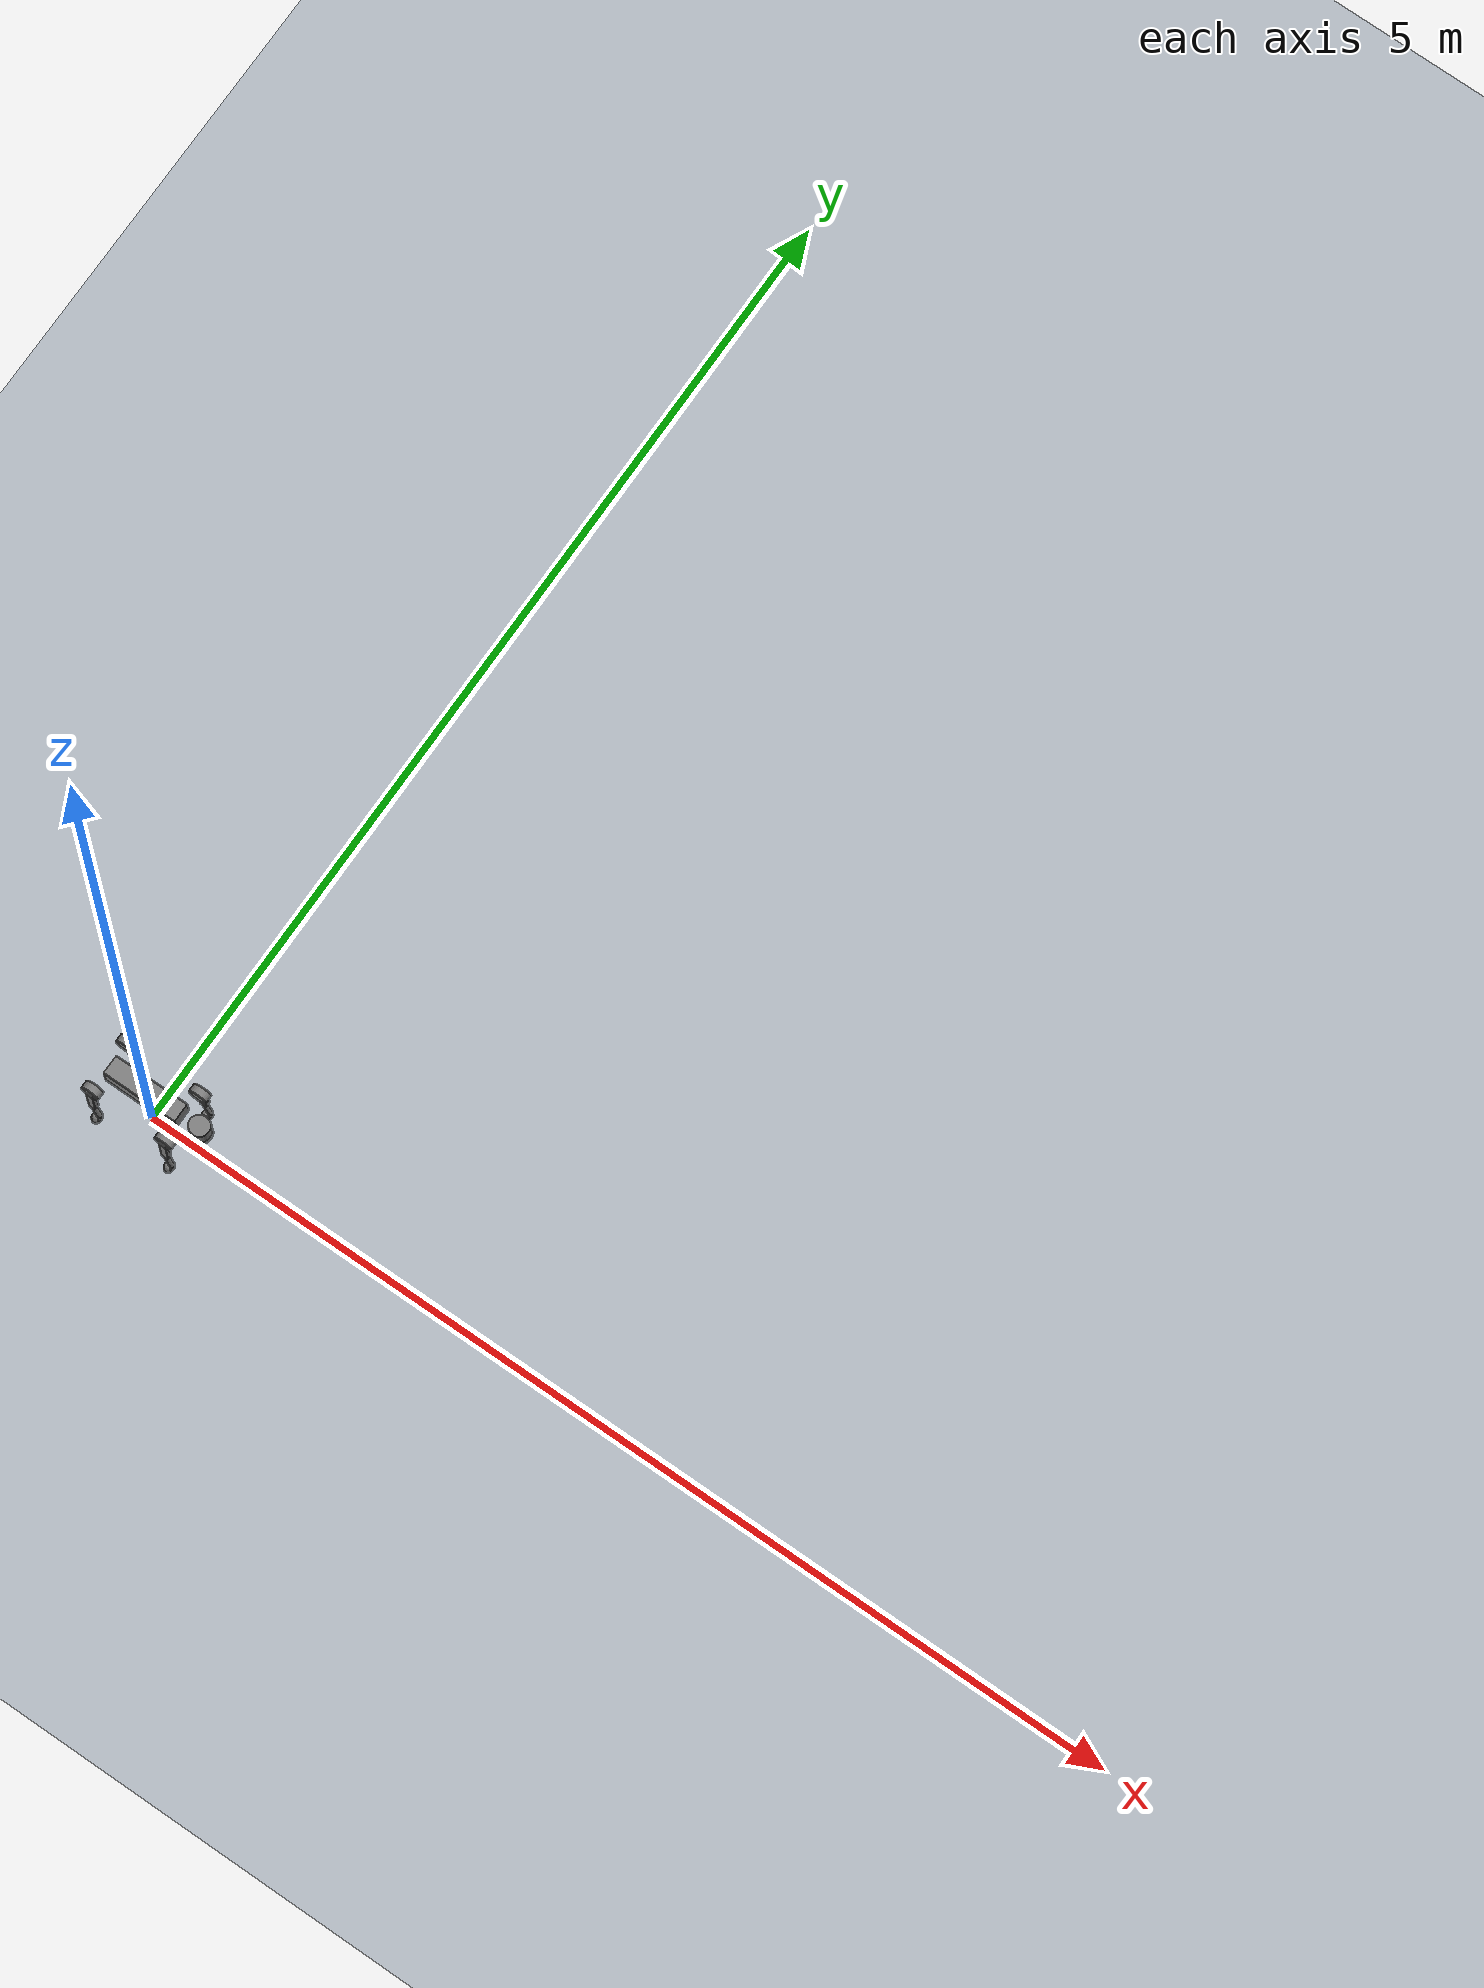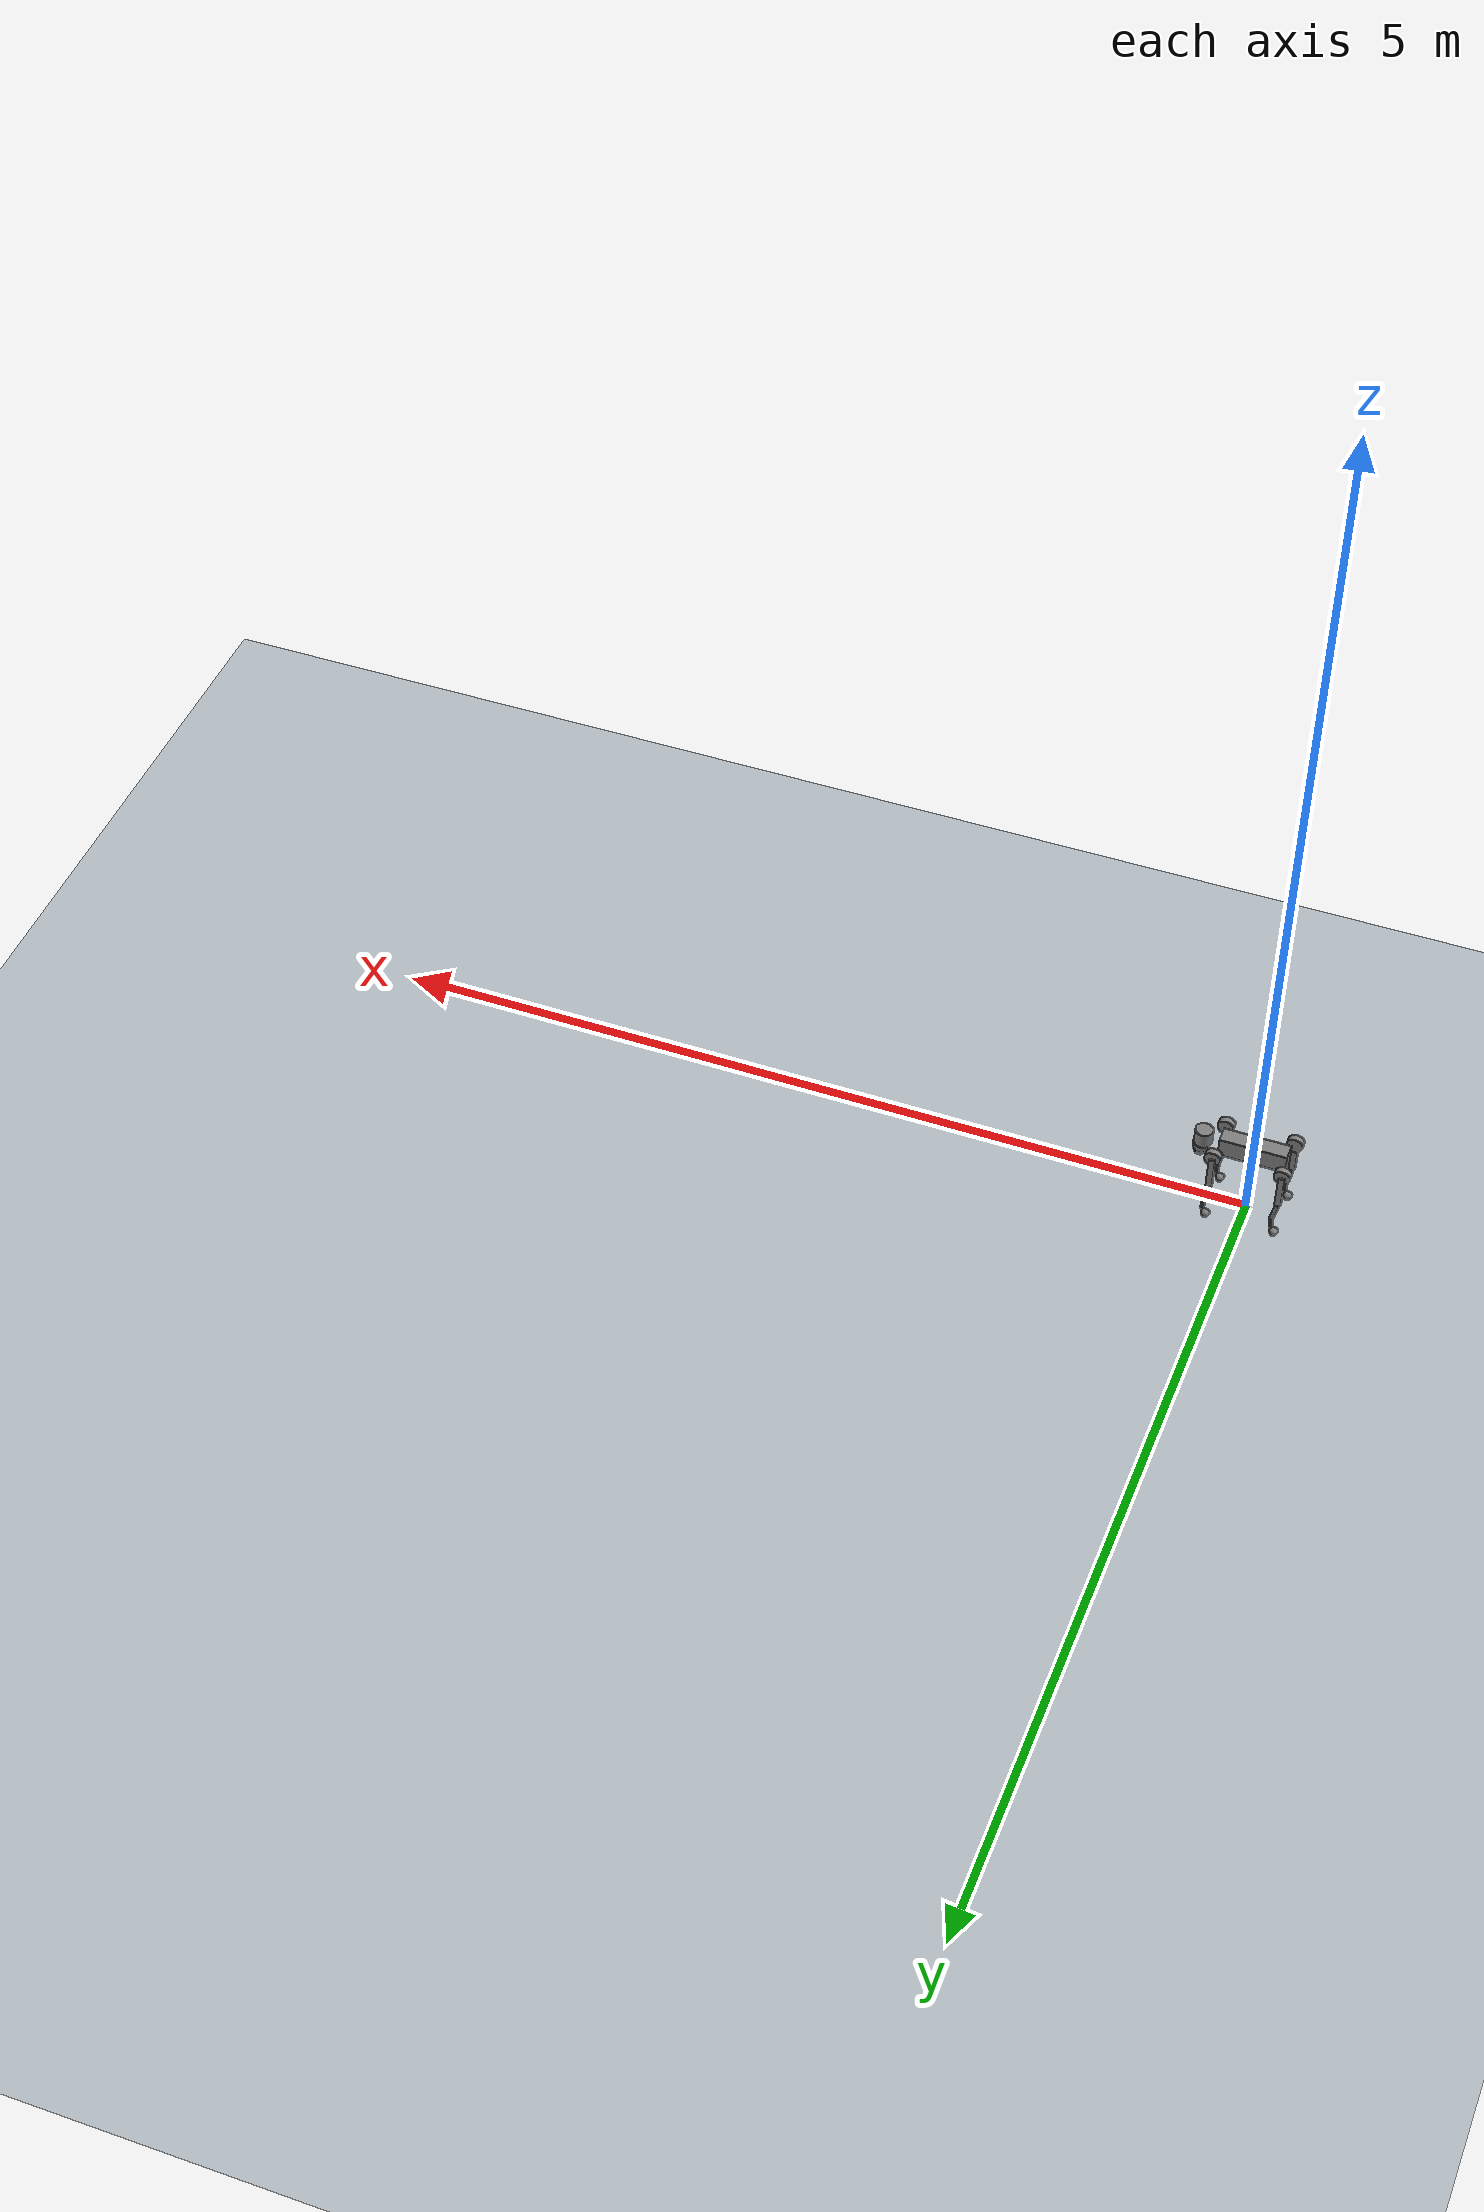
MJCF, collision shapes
<mujoco model="go2 scene">
  <include file="go2.xml" />
  <include file="height_scan_mocap.xml" />

  <statistic center="0 0 0.1" extent="0.8" />

  <visual>
    <headlight diffuse="0.6 0.6 0.6" ambient="0.3 0.3 0.3" specular="0 0 0" />
    <rgba haze="0.15 0.25 0.35 1" />
    <global azimuth="-130" elevation="-20" />
  </visual>

  <asset>
    <texture type="skybox" builtin="gradient" rgb1="0.3 0.5 0.7" rgb2="0 0 0" width="512"
      height="3072" />
    <texture type="2d" name="groundplane" builtin="checker" mark="edge" rgb1="0.2 0.3 0.4"
      rgb2="0.1 0.2 0.3" markrgb="0.8 0.8 0.8" width="300" height="300" />
    <material name="groundplane" texture="groundplane" texuniform="true" texrepeat="5 5"
      reflectance="0.2" />
  </asset>

  <worldbody>
    <light pos="0 0 1.5" dir="0 0 -1" directional="true" />
    <geom name="floor" size="0 0 0.05" type="plane" material="groundplane" />
  </worldbody>
</mujoco>

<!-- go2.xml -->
<mujoco model="go2">
  <compiler angle="radian" meshdir="assets" autolimits="true" />

  <option cone="elliptic" impratio="100" />

  <default>
    <default class="go2">
      <geom friction="0.4" margin="0.001" condim="1"/>
      <joint axis="0 1 0" damping="0.1" armature="0.01" frictionloss="0.2"/>
      <motor ctrlrange="-23.7 23.7"/>
      <default class="abduction">
        <joint axis="1 0 0" range="-1.0472 1.0472"/>
      </default>
      <default class="hip">
        <default class="front_hip">
          <joint range="-1.5708 3.4907"/>
        </default>
        <default class="back_hip">
          <joint range="-0.5236 4.5379"/>
        </default>
      </default>
      <default class="knee">
        <joint range="-2.7227 -0.83776"/>
        <motor ctrlrange="-45.43 45.43"/>
      </default>
      <default class="visual">
        <geom type="mesh" contype="0" conaffinity="0" group="2"/>
      </default>
      <default class="collision">
        <geom group="3"/>
        <default class="foot">
          <geom size="0.022" pos="-0.002 0 -0.213" priority="1" condim="6"
            friction="0.4 0.02 0.01"/>
        </default>
      </default>
    </default>
  </default>

  <asset>
    <material name="metal" rgba=".9 .95 .95 1" />
    <material name="black" rgba="0 0 0 1" />
    <material name="white" rgba="1 1 1 1" />
    <material name="gray" rgba="0.671705 0.692426 0.774270 1" />

    <mesh name="mid360_fov" file="mid360_fov.stl" scale="0.001 0.001 0.001" />

    <mesh file="base_0.obj" />
    <mesh file="base_1.obj" />
    <mesh file="base_2.obj" />
    <mesh file="base_3.obj" />
    <mesh file="base_4.obj" />
    <mesh file="hip_0.obj" />
    <mesh file="hip_1.obj" />
    <mesh file="thigh_0.obj" />
    <mesh file="thigh_1.obj" />
    <mesh file="thigh_mirror_0.obj" />
    <mesh file="thigh_mirror_1.obj" />
    <mesh file="calf_0.obj" />
    <mesh file="calf_1.obj" />
    <mesh file="calf_mirror_0.obj" />
    <mesh file="calf_mirror_1.obj" />
    <mesh file="foot.obj" />
  </asset>

  <worldbody>
    <body name="base_link" pos="0 0 0.445" childclass="go2">
      <inertial pos="0.021112 0 -0.005366" quat="-0.000543471 0.713435 -0.00173769 0.700719"
        mass="6.921"
        diaginertia="0.107027 0.0980771 0.0244531" />
      <freejoint />
      <geom mesh="base_0" material="black" class="visual" />
      <geom mesh="base_1" material="black" class="visual" />
      <geom mesh="base_2" material="black" class="visual" />
      <geom mesh="base_3" material="white" class="visual" />
      <geom mesh="base_4" material="gray" class="visual" />
      <geom size="0.1881 0.04675 0.057" type="box" class="collision" />
      <geom size="0.05 0.045" pos="0.285 0 0.01" type="cylinder" class="collision" />
      <geom size="0.047" pos="0.293 0 -0.06" class="collision" />
      <site name="imu" pos="-0.02557 0 0.04232" />
      <geom name="mid360_visual" type="cylinder" size="0.033 0.033" pos="0.295 0.0 -0.075"
        rgba="0.15 0.15 0.15 1" contype="0" conaffinity="0" group="2" />
      <site name="livox_mid360" pos="0.295 0.0 -0.075" quat="0 1 0 0"
        size="0.01" rgba="1 0 0 1" group="5" />
      <body name="FL_hip" pos="0.1934 0.0465 0">
        <inertial pos="-0.0054 0.00194 -0.000105" quat="0.497014 0.499245 0.505462 0.498237"
          mass="0.678"
          diaginertia="0.00088403 0.000596003 0.000479967" />
        <joint name="FL_hip_joint" class="abduction" />
        <geom mesh="hip_0" material="metal" class="visual" />
        <geom mesh="hip_1" material="gray" class="visual" />
        <geom size="0.046 0.02" pos="0 0.08 0" quat="1 1 0 0" type="cylinder" class="collision" />
        <body name="FL_thigh" pos="0 0.0955 0">
          <inertial pos="-0.00374 -0.0223 -0.0327" quat="0.829533 0.0847635 -0.0200632 0.551623"
            mass="1.152"
            diaginertia="0.00594973 0.00584149 0.000878787" />
          <joint name="FL_thigh_joint" class="front_hip" />
          <geom mesh="thigh_0" material="metal" class="visual" />
          <geom mesh="thigh_1" material="gray" class="visual" />
          <geom size="0.1065 0.01225 0.017" pos="0 0 -0.1065" quat="0.707107 0 0.707107 0"
            type="box" class="collision" />
          <body name="FL_calf" pos="0 0 -0.213">
            <inertial pos="0.00629595 -0.000622121 -0.141417"
              quat="0.710672 0.00154099 -0.00450087 0.703508"
              mass="0.241352" diaginertia="0.0014901 0.00146356 5.31397e-05" />
            <joint name="FL_calf_joint" class="knee" />
            <geom mesh="calf_0" material="gray" class="visual" />
            <geom mesh="calf_1" material="black" class="visual" />
            <geom size="0.012 0.06" pos="0.008 0 -0.06" quat="0.994493 0 -0.104807 0"
              type="cylinder" class="collision" />
            <geom size="0.011 0.0325" pos="0.02 0 -0.148" quat="0.999688 0 0.0249974 0"
              type="cylinder" class="collision" />
            <geom pos="0 0 -0.213" mesh="foot" class="visual" material="black" />
            <geom name="FL" class="foot" />
            <site name="FL_foot_site" pos="-0.002 0 -0.213" size="0.025" />
            <body name="FL_foot" pos="0 0 -0.213" />
          </body>
        </body>
      </body>
      <body name="FR_hip" pos="0.1934 -0.0465 0">
        <inertial pos="-0.0054 -0.00194 -0.000105" quat="0.498237 0.505462 0.499245 0.497014"
          mass="0.678"
          diaginertia="0.00088403 0.000596003 0.000479967" />
        <joint name="FR_hip_joint" class="abduction" />
        <geom mesh="hip_0" material="metal" class="visual" quat="4.63268e-05 1 0 0" />
        <geom mesh="hip_1" material="gray" class="visual" quat="4.63268e-05 1 0 0" />
        <geom size="0.046 0.02" pos="0 -0.08 0" quat="0.707107 0.707107 0 0" type="cylinder"
          class="collision" />
        <body name="FR_thigh" pos="0 -0.0955 0">
          <inertial pos="-0.00374 0.0223 -0.0327" quat="0.551623 -0.0200632 0.0847635 0.829533"
            mass="1.152"
            diaginertia="0.00594973 0.00584149 0.000878787" />
          <joint name="FR_thigh_joint" class="front_hip" />
          <geom mesh="thigh_mirror_0" material="metal" class="visual" />
          <geom mesh="thigh_mirror_1" material="gray" class="visual" />
          <geom size="0.1065 0.01225 0.017" pos="0 0 -0.1065" quat="0.707107 0 0.707107 0"
            type="box" class="collision" />
          <body name="FR_calf" pos="0 0 -0.213">
            <inertial pos="0.00629595 0.000622121 -0.141417"
              quat="0.703508 -0.00450087 0.00154099 0.710672"
              mass="0.241352" diaginertia="0.0014901 0.00146356 5.31397e-05" />
            <joint name="FR_calf_joint" class="knee" />
            <geom mesh="calf_mirror_0" material="gray" class="visual" />
            <geom mesh="calf_mirror_1" material="black" class="visual" />
            <geom size="0.013 0.06" pos="0.01 0 -0.06" quat="0.995004 0 -0.0998334 0"
              type="cylinder" class="collision" />
            <geom size="0.011 0.0325" pos="0.02 0 -0.148" quat="0.999688 0 0.0249974 0"
              type="cylinder" class="collision" />
            <geom pos="0 0 -0.213" mesh="foot" class="visual" material="black" />
            <geom name="FR" class="foot" />
            <site name="FR_foot_site" pos="-0.002 0 -0.213" size="0.025" />
            <body name="FR_foot" pos="0 0 -0.213" />
          </body>
        </body>
      </body>
      <body name="RL_hip" pos="-0.1934 0.0465 0">
        <inertial pos="0.0054 0.00194 -0.000105" quat="0.505462 0.498237 0.497014 0.499245"
          mass="0.678"
          diaginertia="0.00088403 0.000596003 0.000479967" />
        <joint name="RL_hip_joint" class="abduction" />
        <geom mesh="hip_0" material="metal" class="visual" quat="4.63268e-05 0 1 0" />
        <geom mesh="hip_1" material="gray" class="visual" quat="4.63268e-05 0 1 0" />
        <geom size="0.046 0.02" pos="0 0.08 0" quat="0.707107 0.707107 0 0" type="cylinder"
          class="collision" />
        <body name="RL_thigh" pos="0 0.0955 0">
          <inertial pos="-0.00374 -0.0223 -0.0327" quat="0.829533 0.0847635 -0.0200632 0.551623"
            mass="1.152"
            diaginertia="0.00594973 0.00584149 0.000878787" />
          <joint name="RL_thigh_joint" class="back_hip" />
          <geom mesh="thigh_0" material="metal" class="visual" />
          <geom mesh="thigh_1" material="gray" class="visual" />
          <geom size="0.1065 0.01225 0.017" pos="0 0 -0.1065" quat="0.707107 0 0.707107 0"
            type="box" class="collision" />
          <body name="RL_calf" pos="0 0 -0.213">
            <inertial pos="0.00629595 -0.000622121 -0.141417"
              quat="0.710672 0.00154099 -0.00450087 0.703508"
              mass="0.241352" diaginertia="0.0014901 0.00146356 5.31397e-05" />
            <joint name="RL_calf_joint" class="knee" />
            <geom mesh="calf_0" material="gray" class="visual" />
            <geom mesh="calf_1" material="black" class="visual" />
            <geom size="0.013 0.06" pos="0.01 0 -0.06" quat="0.995004 0 -0.0998334 0"
              type="cylinder" class="collision" />
            <geom size="0.011 0.0325" pos="0.02 0 -0.148" quat="0.999688 0 0.0249974 0"
              type="cylinder" class="collision" />
            <geom pos="0 0 -0.213" mesh="foot" class="visual" material="black" />
            <geom name="RL" class="foot" />
            <site name="RL_foot_site" pos="-0.002 0 -0.213" size="0.025" />
            <body name="RL_foot" pos="0 0 -0.213" />
          </body>
        </body>
      </body>
      <body name="RR_hip" pos="-0.1934 -0.0465 0">
        <inertial pos="0.0054 -0.00194 -0.000105" quat="0.499245 0.497014 0.498237 0.505462"
          mass="0.678"
          diaginertia="0.00088403 0.000596003 0.000479967" />
        <joint name="RR_hip_joint" class="abduction" />
        <geom mesh="hip_0" material="metal" class="visual"
          quat="2.14617e-09 4.63268e-05 4.63268e-05 -1" />
        <geom mesh="hip_1" material="gray" class="visual"
          quat="2.14617e-09 4.63268e-05 4.63268e-05 -1" />
        <geom size="0.046 0.02" pos="0 -0.08 0" quat="0.707107 0.707107 0 0" type="cylinder"
          class="collision" />
        <body name="RR_thigh" pos="0 -0.0955 0">
          <inertial pos="-0.00374 0.0223 -0.0327" quat="0.551623 -0.0200632 0.0847635 0.829533"
            mass="1.152"
            diaginertia="0.00594973 0.00584149 0.000878787" />
          <joint name="RR_thigh_joint" class="back_hip" />
          <geom mesh="thigh_mirror_0" material="metal" class="visual" />
          <geom mesh="thigh_mirror_1" material="gray" class="visual" />
          <geom size="0.1065 0.01225 0.017" pos="0 0 -0.1065" quat="0.707107 0 0.707107 0"
            type="box" class="collision" />
          <body name="RR_calf" pos="0 0 -0.213">
            <inertial pos="0.00629595 0.000622121 -0.141417"
              quat="0.703508 -0.00450087 0.00154099 0.710672"
              mass="0.241352" diaginertia="0.0014901 0.00146356 5.31397e-05" />
            <joint name="RR_calf_joint" class="knee" />
            <geom mesh="calf_mirror_0" material="gray" class="visual" />
            <geom mesh="calf_mirror_1" material="black" class="visual" />
            <geom size="0.013 0.06" pos="0.01 0 -0.06" quat="0.995004 0 -0.0998334 0"
              type="cylinder" class="collision" />
            <geom size="0.011 0.0325" pos="0.02 0 -0.148" quat="0.999688 0 0.0249974 0"
              type="cylinder" class="collision" />
            <geom pos="0 0 -0.213" mesh="foot" class="visual" material="black" />
            <geom name="RR" class="foot" />
            <site name="RR_foot_site" pos="-0.002 0 -0.213" size="0.025" />
            <body name="RR_foot" pos="0 0 -0.213" />
          </body>
        </body>
      </body>
    </body>
  </worldbody>

  <actuator>
    <motor class="abduction" name="FR_hip" joint="FR_hip_joint" />
    <motor class="hip" name="FR_thigh" joint="FR_thigh_joint" />
    <motor class="knee" name="FR_calf" joint="FR_calf_joint" />
    <motor class="abduction" name="FL_hip" joint="FL_hip_joint" />
    <motor class="hip" name="FL_thigh" joint="FL_thigh_joint" />
    <motor class="knee" name="FL_calf" joint="FL_calf_joint" />
    <motor class="abduction" name="RR_hip" joint="RR_hip_joint" />
    <motor class="hip" name="RR_thigh" joint="RR_thigh_joint" />
    <motor class="knee" name="RR_calf" joint="RR_calf_joint" />
    <motor class="abduction" name="RL_hip" joint="RL_hip_joint" />
    <motor class="hip" name="RL_thigh" joint="RL_thigh_joint" />
    <motor class="knee" name="RL_calf" joint="RL_calf_joint" />
  </actuator>

  <sensor>
    <jointpos name="FR_hip_pos" joint="FR_hip_joint" />
    <jointpos name="FR_thigh_pos" joint="FR_thigh_joint" />
    <jointpos name="FR_calf_pos" joint="FR_calf_joint" />
    <jointpos name="FL_hip_pos" joint="FL_hip_joint" />
    <jointpos name="FL_thigh_pos" joint="FL_thigh_joint" />
    <jointpos name="FL_calf_pos" joint="FL_calf_joint" />
    <jointpos name="RR_hip_pos" joint="RR_hip_joint" />
    <jointpos name="RR_thigh_pos" joint="RR_thigh_joint" />
    <jointpos name="RR_calf_pos" joint="RR_calf_joint" />
    <jointpos name="RL_hip_pos" joint="RL_hip_joint" />
    <jointpos name="RL_thigh_pos" joint="RL_thigh_joint" />
    <jointpos name="RL_calf_pos" joint="RL_calf_joint" />

    <jointvel name="FR_hip_vel" joint="FR_hip_joint" />
    <jointvel name="FR_thigh_vel" joint="FR_thigh_joint" />
    <jointvel name="FR_calf_vel" joint="FR_calf_joint" />
    <jointvel name="FL_hip_vel" joint="FL_hip_joint" />
    <jointvel name="FL_thigh_vel" joint="FL_thigh_joint" />
    <jointvel name="FL_calf_vel" joint="FL_calf_joint" />
    <jointvel name="RR_hip_vel" joint="RR_hip_joint" />
    <jointvel name="RR_thigh_vel" joint="RR_thigh_joint" />
    <jointvel name="RR_calf_vel" joint="RR_calf_joint" />
    <jointvel name="RL_hip_vel" joint="RL_hip_joint" />
    <jointvel name="RL_thigh_vel" joint="RL_thigh_joint" />
    <jointvel name="RL_calf_vel" joint="RL_calf_joint" />

    <jointactuatorfrc name="FR_hip_torque" joint="FR_hip_joint" noise="0.01" />
    <jointactuatorfrc name="FR_thigh_torque" joint="FR_thigh_joint" noise="0.01" />
    <jointactuatorfrc name="FR_calf_torque" joint="FR_calf_joint" noise="0.01" />
    <jointactuatorfrc name="FL_hip_torque" joint="FL_hip_joint" noise="0.01" />
    <jointactuatorfrc name="FL_thigh_torque" joint="FL_thigh_joint" noise="0.01" />
    <jointactuatorfrc name="FL_calf_torque" joint="FL_calf_joint" noise="0.01" />
    <jointactuatorfrc name="RR_hip_torque" joint="RR_hip_joint" noise="0.01" />
    <jointactuatorfrc name="RR_thigh_torque" joint="RR_thigh_joint" noise="0.01" />
    <jointactuatorfrc name="RR_calf_torque" joint="RR_calf_joint" noise="0.01" />
    <jointactuatorfrc name="RL_hip_torque" joint="RL_hip_joint" noise="0.01" />
    <jointactuatorfrc name="RL_thigh_torque" joint="RL_thigh_joint" noise="0.01" />
    <jointactuatorfrc name="RL_calf_torque" joint="RL_calf_joint" noise="0.01" />

    <framequat name="imu_quat" objtype="site" objname="imu" />
    <gyro name="imu_gyro" site="imu" />
    <accelerometer name="imu_acc" site="imu" />

    <framepos name="frame_pos" objtype="site" objname="imu" />
    <framelinvel name="frame_vel" objtype="site" objname="imu" />

    <framequat name="mid360_imu_quat" objtype="site" objname="livox_mid360" />
    <gyro name="mid360_imu_gyro" site="livox_mid360" />
    <accelerometer name="mid360_imu_acc" site="livox_mid360" />

    <touch name="FR_foot_force" site="FR_foot_site" />
    <touch name="FL_foot_force" site="FL_foot_site" />
    <touch name="RR_foot_force" site="RR_foot_site" />
    <touch name="RL_foot_force" site="RL_foot_site" />
  </sensor>

  <keyframe>
    <key name="home" qpos="0 0 0.27 1 0 0 0 0 0.9 -1.8 0 0.9 -1.8 0 0.9 -1.8 0 0.9 -1.8"
      ctrl="0 0.9 -1.8 0 0.9 -1.8 0 0.9 -1.8 0 0.9 -1.8" />
  </keyframe>
</mujoco>

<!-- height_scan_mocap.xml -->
<mujoco model="height_scan_mocap">
  <worldbody>
    <body mocap="true" name="hs_000" pos="0 0 -10"><geom type="sphere" size="0.02" rgba="0.95 0.15 0.1 0.85" contype="0" conaffinity="0" group="2"/></body>
    <body mocap="true" name="hs_001" pos="0 0 -10"><geom type="sphere" size="0.02" rgba="0.95 0.15 0.1 0.85" contype="0" conaffinity="0" group="2"/></body>
    <body mocap="true" name="hs_002" pos="0 0 -10"><geom type="sphere" size="0.02" rgba="0.95 0.15 0.1 0.85" contype="0" conaffinity="0" group="2"/></body>
    <body mocap="true" name="hs_003" pos="0 0 -10"><geom type="sphere" size="0.02" rgba="0.95 0.15 0.1 0.85" contype="0" conaffinity="0" group="2"/></body>
    <body mocap="true" name="hs_004" pos="0 0 -10"><geom type="sphere" size="0.02" rgba="0.95 0.15 0.1 0.85" contype="0" conaffinity="0" group="2"/></body>
    <body mocap="true" name="hs_005" pos="0 0 -10"><geom type="sphere" size="0.02" rgba="0.95 0.15 0.1 0.85" contype="0" conaffinity="0" group="2"/></body>
    <body mocap="true" name="hs_006" pos="0 0 -10"><geom type="sphere" size="0.02" rgba="0.95 0.15 0.1 0.85" contype="0" conaffinity="0" group="2"/></body>
    <body mocap="true" name="hs_007" pos="0 0 -10"><geom type="sphere" size="0.02" rgba="0.95 0.15 0.1 0.85" contype="0" conaffinity="0" group="2"/></body>
    <body mocap="true" name="hs_008" pos="0 0 -10"><geom type="sphere" size="0.02" rgba="0.95 0.15 0.1 0.85" contype="0" conaffinity="0" group="2"/></body>
    <body mocap="true" name="hs_009" pos="0 0 -10"><geom type="sphere" size="0.02" rgba="0.95 0.15 0.1 0.85" contype="0" conaffinity="0" group="2"/></body>
    <body mocap="true" name="hs_010" pos="0 0 -10"><geom type="sphere" size="0.02" rgba="0.95 0.15 0.1 0.85" contype="0" conaffinity="0" group="2"/></body>
    <body mocap="true" name="hs_011" pos="0 0 -10"><geom type="sphere" size="0.02" rgba="0.95 0.15 0.1 0.85" contype="0" conaffinity="0" group="2"/></body>
    <body mocap="true" name="hs_012" pos="0 0 -10"><geom type="sphere" size="0.02" rgba="0.95 0.15 0.1 0.85" contype="0" conaffinity="0" group="2"/></body>
    <body mocap="true" name="hs_013" pos="0 0 -10"><geom type="sphere" size="0.02" rgba="0.95 0.15 0.1 0.85" contype="0" conaffinity="0" group="2"/></body>
    <body mocap="true" name="hs_014" pos="0 0 -10"><geom type="sphere" size="0.02" rgba="0.95 0.15 0.1 0.85" contype="0" conaffinity="0" group="2"/></body>
    <body mocap="true" name="hs_015" pos="0 0 -10"><geom type="sphere" size="0.02" rgba="0.95 0.15 0.1 0.85" contype="0" conaffinity="0" group="2"/></body>
    <body mocap="true" name="hs_016" pos="0 0 -10"><geom type="sphere" size="0.02" rgba="0.95 0.15 0.1 0.85" contype="0" conaffinity="0" group="2"/></body>
    <body mocap="true" name="hs_017" pos="0 0 -10"><geom type="sphere" size="0.02" rgba="0.95 0.15 0.1 0.85" contype="0" conaffinity="0" group="2"/></body>
    <body mocap="true" name="hs_018" pos="0 0 -10"><geom type="sphere" size="0.02" rgba="0.95 0.15 0.1 0.85" contype="0" conaffinity="0" group="2"/></body>
    <body mocap="true" name="hs_019" pos="0 0 -10"><geom type="sphere" size="0.02" rgba="0.95 0.15 0.1 0.85" contype="0" conaffinity="0" group="2"/></body>
    <body mocap="true" name="hs_020" pos="0 0 -10"><geom type="sphere" size="0.02" rgba="0.95 0.15 0.1 0.85" contype="0" conaffinity="0" group="2"/></body>
    <body mocap="true" name="hs_021" pos="0 0 -10"><geom type="sphere" size="0.02" rgba="0.95 0.15 0.1 0.85" contype="0" conaffinity="0" group="2"/></body>
    <body mocap="true" name="hs_022" pos="0 0 -10"><geom type="sphere" size="0.02" rgba="0.95 0.15 0.1 0.85" contype="0" conaffinity="0" group="2"/></body>
    <body mocap="true" name="hs_023" pos="0 0 -10"><geom type="sphere" size="0.02" rgba="0.95 0.15 0.1 0.85" contype="0" conaffinity="0" group="2"/></body>
    <body mocap="true" name="hs_024" pos="0 0 -10"><geom type="sphere" size="0.02" rgba="0.95 0.15 0.1 0.85" contype="0" conaffinity="0" group="2"/></body>
    <body mocap="true" name="hs_025" pos="0 0 -10"><geom type="sphere" size="0.02" rgba="0.95 0.15 0.1 0.85" contype="0" conaffinity="0" group="2"/></body>
    <body mocap="true" name="hs_026" pos="0 0 -10"><geom type="sphere" size="0.02" rgba="0.95 0.15 0.1 0.85" contype="0" conaffinity="0" group="2"/></body>
    <body mocap="true" name="hs_027" pos="0 0 -10"><geom type="sphere" size="0.02" rgba="0.95 0.15 0.1 0.85" contype="0" conaffinity="0" group="2"/></body>
    <body mocap="true" name="hs_028" pos="0 0 -10"><geom type="sphere" size="0.02" rgba="0.95 0.15 0.1 0.85" contype="0" conaffinity="0" group="2"/></body>
    <body mocap="true" name="hs_029" pos="0 0 -10"><geom type="sphere" size="0.02" rgba="0.95 0.15 0.1 0.85" contype="0" conaffinity="0" group="2"/></body>
    <body mocap="true" name="hs_030" pos="0 0 -10"><geom type="sphere" size="0.02" rgba="0.95 0.15 0.1 0.85" contype="0" conaffinity="0" group="2"/></body>
    <body mocap="true" name="hs_031" pos="0 0 -10"><geom type="sphere" size="0.02" rgba="0.95 0.15 0.1 0.85" contype="0" conaffinity="0" group="2"/></body>
    <body mocap="true" name="hs_032" pos="0 0 -10"><geom type="sphere" size="0.02" rgba="0.95 0.15 0.1 0.85" contype="0" conaffinity="0" group="2"/></body>
    <body mocap="true" name="hs_033" pos="0 0 -10"><geom type="sphere" size="0.02" rgba="0.95 0.15 0.1 0.85" contype="0" conaffinity="0" group="2"/></body>
    <body mocap="true" name="hs_034" pos="0 0 -10"><geom type="sphere" size="0.02" rgba="0.95 0.15 0.1 0.85" contype="0" conaffinity="0" group="2"/></body>
    <body mocap="true" name="hs_035" pos="0 0 -10"><geom type="sphere" size="0.02" rgba="0.95 0.15 0.1 0.85" contype="0" conaffinity="0" group="2"/></body>
    <body mocap="true" name="hs_036" pos="0 0 -10"><geom type="sphere" size="0.02" rgba="0.95 0.15 0.1 0.85" contype="0" conaffinity="0" group="2"/></body>
    <body mocap="true" name="hs_037" pos="0 0 -10"><geom type="sphere" size="0.02" rgba="0.95 0.15 0.1 0.85" contype="0" conaffinity="0" group="2"/></body>
    <body mocap="true" name="hs_038" pos="0 0 -10"><geom type="sphere" size="0.02" rgba="0.95 0.15 0.1 0.85" contype="0" conaffinity="0" group="2"/></body>
    <body mocap="true" name="hs_039" pos="0 0 -10"><geom type="sphere" size="0.02" rgba="0.95 0.15 0.1 0.85" contype="0" conaffinity="0" group="2"/></body>
    <body mocap="true" name="hs_040" pos="0 0 -10"><geom type="sphere" size="0.02" rgba="0.95 0.15 0.1 0.85" contype="0" conaffinity="0" group="2"/></body>
    <body mocap="true" name="hs_041" pos="0 0 -10"><geom type="sphere" size="0.02" rgba="0.95 0.15 0.1 0.85" contype="0" conaffinity="0" group="2"/></body>
    <body mocap="true" name="hs_042" pos="0 0 -10"><geom type="sphere" size="0.02" rgba="0.95 0.15 0.1 0.85" contype="0" conaffinity="0" group="2"/></body>
    <body mocap="true" name="hs_043" pos="0 0 -10"><geom type="sphere" size="0.02" rgba="0.95 0.15 0.1 0.85" contype="0" conaffinity="0" group="2"/></body>
    <body mocap="true" name="hs_044" pos="0 0 -10"><geom type="sphere" size="0.02" rgba="0.95 0.15 0.1 0.85" contype="0" conaffinity="0" group="2"/></body>
    <body mocap="true" name="hs_045" pos="0 0 -10"><geom type="sphere" size="0.02" rgba="0.95 0.15 0.1 0.85" contype="0" conaffinity="0" group="2"/></body>
    <body mocap="true" name="hs_046" pos="0 0 -10"><geom type="sphere" size="0.02" rgba="0.95 0.15 0.1 0.85" contype="0" conaffinity="0" group="2"/></body>
    <body mocap="true" name="hs_047" pos="0 0 -10"><geom type="sphere" size="0.02" rgba="0.95 0.15 0.1 0.85" contype="0" conaffinity="0" group="2"/></body>
    <body mocap="true" name="hs_048" pos="0 0 -10"><geom type="sphere" size="0.02" rgba="0.95 0.15 0.1 0.85" contype="0" conaffinity="0" group="2"/></body>
    <body mocap="true" name="hs_049" pos="0 0 -10"><geom type="sphere" size="0.02" rgba="0.95 0.15 0.1 0.85" contype="0" conaffinity="0" group="2"/></body>
    <body mocap="true" name="hs_050" pos="0 0 -10"><geom type="sphere" size="0.02" rgba="0.95 0.15 0.1 0.85" contype="0" conaffinity="0" group="2"/></body>
    <body mocap="true" name="hs_051" pos="0 0 -10"><geom type="sphere" size="0.02" rgba="0.95 0.15 0.1 0.85" contype="0" conaffinity="0" group="2"/></body>
    <body mocap="true" name="hs_052" pos="0 0 -10"><geom type="sphere" size="0.02" rgba="0.95 0.15 0.1 0.85" contype="0" conaffinity="0" group="2"/></body>
    <body mocap="true" name="hs_053" pos="0 0 -10"><geom type="sphere" size="0.02" rgba="0.95 0.15 0.1 0.85" contype="0" conaffinity="0" group="2"/></body>
    <body mocap="true" name="hs_054" pos="0 0 -10"><geom type="sphere" size="0.02" rgba="0.95 0.15 0.1 0.85" contype="0" conaffinity="0" group="2"/></body>
    <body mocap="true" name="hs_055" pos="0 0 -10"><geom type="sphere" size="0.02" rgba="0.95 0.15 0.1 0.85" contype="0" conaffinity="0" group="2"/></body>
    <body mocap="true" name="hs_056" pos="0 0 -10"><geom type="sphere" size="0.02" rgba="0.95 0.15 0.1 0.85" contype="0" conaffinity="0" group="2"/></body>
    <body mocap="true" name="hs_057" pos="0 0 -10"><geom type="sphere" size="0.02" rgba="0.95 0.15 0.1 0.85" contype="0" conaffinity="0" group="2"/></body>
    <body mocap="true" name="hs_058" pos="0 0 -10"><geom type="sphere" size="0.02" rgba="0.95 0.15 0.1 0.85" contype="0" conaffinity="0" group="2"/></body>
    <body mocap="true" name="hs_059" pos="0 0 -10"><geom type="sphere" size="0.02" rgba="0.95 0.15 0.1 0.85" contype="0" conaffinity="0" group="2"/></body>
    <body mocap="true" name="hs_060" pos="0 0 -10"><geom type="sphere" size="0.02" rgba="0.95 0.15 0.1 0.85" contype="0" conaffinity="0" group="2"/></body>
    <body mocap="true" name="hs_061" pos="0 0 -10"><geom type="sphere" size="0.02" rgba="0.95 0.15 0.1 0.85" contype="0" conaffinity="0" group="2"/></body>
    <body mocap="true" name="hs_062" pos="0 0 -10"><geom type="sphere" size="0.02" rgba="0.95 0.15 0.1 0.85" contype="0" conaffinity="0" group="2"/></body>
    <body mocap="true" name="hs_063" pos="0 0 -10"><geom type="sphere" size="0.02" rgba="0.95 0.15 0.1 0.85" contype="0" conaffinity="0" group="2"/></body>
    <body mocap="true" name="hs_064" pos="0 0 -10"><geom type="sphere" size="0.02" rgba="0.95 0.15 0.1 0.85" contype="0" conaffinity="0" group="2"/></body>
    <body mocap="true" name="hs_065" pos="0 0 -10"><geom type="sphere" size="0.02" rgba="0.95 0.15 0.1 0.85" contype="0" conaffinity="0" group="2"/></body>
    <body mocap="true" name="hs_066" pos="0 0 -10"><geom type="sphere" size="0.02" rgba="0.95 0.15 0.1 0.85" contype="0" conaffinity="0" group="2"/></body>
    <body mocap="true" name="hs_067" pos="0 0 -10"><geom type="sphere" size="0.02" rgba="0.95 0.15 0.1 0.85" contype="0" conaffinity="0" group="2"/></body>
    <body mocap="true" name="hs_068" pos="0 0 -10"><geom type="sphere" size="0.02" rgba="0.95 0.15 0.1 0.85" contype="0" conaffinity="0" group="2"/></body>
    <body mocap="true" name="hs_069" pos="0 0 -10"><geom type="sphere" size="0.02" rgba="0.95 0.15 0.1 0.85" contype="0" conaffinity="0" group="2"/></body>
    <body mocap="true" name="hs_070" pos="0 0 -10"><geom type="sphere" size="0.02" rgba="0.95 0.15 0.1 0.85" contype="0" conaffinity="0" group="2"/></body>
    <body mocap="true" name="hs_071" pos="0 0 -10"><geom type="sphere" size="0.02" rgba="0.95 0.15 0.1 0.85" contype="0" conaffinity="0" group="2"/></body>
    <body mocap="true" name="hs_072" pos="0 0 -10"><geom type="sphere" size="0.02" rgba="0.95 0.15 0.1 0.85" contype="0" conaffinity="0" group="2"/></body>
    <body mocap="true" name="hs_073" pos="0 0 -10"><geom type="sphere" size="0.02" rgba="0.95 0.15 0.1 0.85" contype="0" conaffinity="0" group="2"/></body>
    <body mocap="true" name="hs_074" pos="0 0 -10"><geom type="sphere" size="0.02" rgba="0.95 0.15 0.1 0.85" contype="0" conaffinity="0" group="2"/></body>
    <body mocap="true" name="hs_075" pos="0 0 -10"><geom type="sphere" size="0.02" rgba="0.95 0.15 0.1 0.85" contype="0" conaffinity="0" group="2"/></body>
    <body mocap="true" name="hs_076" pos="0 0 -10"><geom type="sphere" size="0.02" rgba="0.95 0.15 0.1 0.85" contype="0" conaffinity="0" group="2"/></body>
    <body mocap="true" name="hs_077" pos="0 0 -10"><geom type="sphere" size="0.02" rgba="0.95 0.15 0.1 0.85" contype="0" conaffinity="0" group="2"/></body>
    <body mocap="true" name="hs_078" pos="0 0 -10"><geom type="sphere" size="0.02" rgba="0.95 0.15 0.1 0.85" contype="0" conaffinity="0" group="2"/></body>
    <body mocap="true" name="hs_079" pos="0 0 -10"><geom type="sphere" size="0.02" rgba="0.95 0.15 0.1 0.85" contype="0" conaffinity="0" group="2"/></body>
    <body mocap="true" name="hs_080" pos="0 0 -10"><geom type="sphere" size="0.02" rgba="0.95 0.15 0.1 0.85" contype="0" conaffinity="0" group="2"/></body>
    <body mocap="true" name="hs_081" pos="0 0 -10"><geom type="sphere" size="0.02" rgba="0.95 0.15 0.1 0.85" contype="0" conaffinity="0" group="2"/></body>
    <body mocap="true" name="hs_082" pos="0 0 -10"><geom type="sphere" size="0.02" rgba="0.95 0.15 0.1 0.85" contype="0" conaffinity="0" group="2"/></body>
    <body mocap="true" name="hs_083" pos="0 0 -10"><geom type="sphere" size="0.02" rgba="0.95 0.15 0.1 0.85" contype="0" conaffinity="0" group="2"/></body>
    <body mocap="true" name="hs_084" pos="0 0 -10"><geom type="sphere" size="0.02" rgba="0.95 0.15 0.1 0.85" contype="0" conaffinity="0" group="2"/></body>
    <body mocap="true" name="hs_085" pos="0 0 -10"><geom type="sphere" size="0.02" rgba="0.95 0.15 0.1 0.85" contype="0" conaffinity="0" group="2"/></body>
    <body mocap="true" name="hs_086" pos="0 0 -10"><geom type="sphere" size="0.02" rgba="0.95 0.15 0.1 0.85" contype="0" conaffinity="0" group="2"/></body>
    <body mocap="true" name="hs_087" pos="0 0 -10"><geom type="sphere" size="0.02" rgba="0.95 0.15 0.1 0.85" contype="0" conaffinity="0" group="2"/></body>
    <body mocap="true" name="hs_088" pos="0 0 -10"><geom type="sphere" size="0.02" rgba="0.95 0.15 0.1 0.85" contype="0" conaffinity="0" group="2"/></body>
    <body mocap="true" name="hs_089" pos="0 0 -10"><geom type="sphere" size="0.02" rgba="0.95 0.15 0.1 0.85" contype="0" conaffinity="0" group="2"/></body>
    <body mocap="true" name="hs_090" pos="0 0 -10"><geom type="sphere" size="0.02" rgba="0.95 0.15 0.1 0.85" contype="0" conaffinity="0" group="2"/></body>
    <body mocap="true" name="hs_091" pos="0 0 -10"><geom type="sphere" size="0.02" rgba="0.95 0.15 0.1 0.85" contype="0" conaffinity="0" group="2"/></body>
    <body mocap="true" name="hs_092" pos="0 0 -10"><geom type="sphere" size="0.02" rgba="0.95 0.15 0.1 0.85" contype="0" conaffinity="0" group="2"/></body>
    <body mocap="true" name="hs_093" pos="0 0 -10"><geom type="sphere" size="0.02" rgba="0.95 0.15 0.1 0.85" contype="0" conaffinity="0" group="2"/></body>
    <body mocap="true" name="hs_094" pos="0 0 -10"><geom type="sphere" size="0.02" rgba="0.95 0.15 0.1 0.85" contype="0" conaffinity="0" group="2"/></body>
    <body mocap="true" name="hs_095" pos="0 0 -10"><geom type="sphere" size="0.02" rgba="0.95 0.15 0.1 0.85" contype="0" conaffinity="0" group="2"/></body>
    <body mocap="true" name="hs_096" pos="0 0 -10"><geom type="sphere" size="0.02" rgba="0.95 0.15 0.1 0.85" contype="0" conaffinity="0" group="2"/></body>
    <body mocap="true" name="hs_097" pos="0 0 -10"><geom type="sphere" size="0.02" rgba="0.95 0.15 0.1 0.85" contype="0" conaffinity="0" group="2"/></body>
    <body mocap="true" name="hs_098" pos="0 0 -10"><geom type="sphere" size="0.02" rgba="0.95 0.15 0.1 0.85" contype="0" conaffinity="0" group="2"/></body>
    <body mocap="true" name="hs_099" pos="0 0 -10"><geom type="sphere" size="0.02" rgba="0.95 0.15 0.1 0.85" contype="0" conaffinity="0" group="2"/></body>
    <body mocap="true" name="hs_100" pos="0 0 -10"><geom type="sphere" size="0.02" rgba="0.95 0.15 0.1 0.85" contype="0" conaffinity="0" group="2"/></body>
    <body mocap="true" name="hs_101" pos="0 0 -10"><geom type="sphere" size="0.02" rgba="0.95 0.15 0.1 0.85" contype="0" conaffinity="0" group="2"/></body>
    <body mocap="true" name="hs_102" pos="0 0 -10"><geom type="sphere" size="0.02" rgba="0.95 0.15 0.1 0.85" contype="0" conaffinity="0" group="2"/></body>
    <body mocap="true" name="hs_103" pos="0 0 -10"><geom type="sphere" size="0.02" rgba="0.95 0.15 0.1 0.85" contype="0" conaffinity="0" group="2"/></body>
    <body mocap="true" name="hs_104" pos="0 0 -10"><geom type="sphere" size="0.02" rgba="0.95 0.15 0.1 0.85" contype="0" conaffinity="0" group="2"/></body>
    <body mocap="true" name="hs_105" pos="0 0 -10"><geom type="sphere" size="0.02" rgba="0.95 0.15 0.1 0.85" contype="0" conaffinity="0" group="2"/></body>
    <body mocap="true" name="hs_106" pos="0 0 -10"><geom type="sphere" size="0.02" rgba="0.95 0.15 0.1 0.85" contype="0" conaffinity="0" group="2"/></body>
    <body mocap="true" name="hs_107" pos="0 0 -10"><geom type="sphere" size="0.02" rgba="0.95 0.15 0.1 0.85" contype="0" conaffinity="0" group="2"/></body>
    <body mocap="true" name="hs_108" pos="0 0 -10"><geom type="sphere" size="0.02" rgba="0.95 0.15 0.1 0.85" contype="0" conaffinity="0" group="2"/></body>
    <body mocap="true" name="hs_109" pos="0 0 -10"><geom type="sphere" size="0.02" rgba="0.95 0.15 0.1 0.85" contype="0" conaffinity="0" group="2"/></body>
    <body mocap="true" name="hs_110" pos="0 0 -10"><geom type="sphere" size="0.02" rgba="0.95 0.15 0.1 0.85" contype="0" conaffinity="0" group="2"/></body>
    <body mocap="true" name="hs_111" pos="0 0 -10"><geom type="sphere" size="0.02" rgba="0.95 0.15 0.1 0.85" contype="0" conaffinity="0" group="2"/></body>
    <body mocap="true" name="hs_112" pos="0 0 -10"><geom type="sphere" size="0.02" rgba="0.95 0.15 0.1 0.85" contype="0" conaffinity="0" group="2"/></body>
    <body mocap="true" name="hs_113" pos="0 0 -10"><geom type="sphere" size="0.02" rgba="0.95 0.15 0.1 0.85" contype="0" conaffinity="0" group="2"/></body>
    <body mocap="true" name="hs_114" pos="0 0 -10"><geom type="sphere" size="0.02" rgba="0.95 0.15 0.1 0.85" contype="0" conaffinity="0" group="2"/></body>
    <body mocap="true" name="hs_115" pos="0 0 -10"><geom type="sphere" size="0.02" rgba="0.95 0.15 0.1 0.85" contype="0" conaffinity="0" group="2"/></body>
    <body mocap="true" name="hs_116" pos="0 0 -10"><geom type="sphere" size="0.02" rgba="0.95 0.15 0.1 0.85" contype="0" conaffinity="0" group="2"/></body>
    <body mocap="true" name="hs_117" pos="0 0 -10"><geom type="sphere" size="0.02" rgba="0.95 0.15 0.1 0.85" contype="0" conaffinity="0" group="2"/></body>
    <body mocap="true" name="hs_118" pos="0 0 -10"><geom type="sphere" size="0.02" rgba="0.95 0.15 0.1 0.85" contype="0" conaffinity="0" group="2"/></body>
    <body mocap="true" name="hs_119" pos="0 0 -10"><geom type="sphere" size="0.02" rgba="0.95 0.15 0.1 0.85" contype="0" conaffinity="0" group="2"/></body>
    <body mocap="true" name="hs_120" pos="0 0 -10"><geom type="sphere" size="0.02" rgba="0.95 0.15 0.1 0.85" contype="0" conaffinity="0" group="2"/></body>
    <body mocap="true" name="hs_121" pos="0 0 -10"><geom type="sphere" size="0.02" rgba="0.95 0.15 0.1 0.85" contype="0" conaffinity="0" group="2"/></body>
    <body mocap="true" name="hs_122" pos="0 0 -10"><geom type="sphere" size="0.02" rgba="0.95 0.15 0.1 0.85" contype="0" conaffinity="0" group="2"/></body>
    <body mocap="true" name="hs_123" pos="0 0 -10"><geom type="sphere" size="0.02" rgba="0.95 0.15 0.1 0.85" contype="0" conaffinity="0" group="2"/></body>
    <body mocap="true" name="hs_124" pos="0 0 -10"><geom type="sphere" size="0.02" rgba="0.95 0.15 0.1 0.85" contype="0" conaffinity="0" group="2"/></body>
    <body mocap="true" name="hs_125" pos="0 0 -10"><geom type="sphere" size="0.02" rgba="0.95 0.15 0.1 0.85" contype="0" conaffinity="0" group="2"/></body>
    <body mocap="true" name="hs_126" pos="0 0 -10"><geom type="sphere" size="0.02" rgba="0.95 0.15 0.1 0.85" contype="0" conaffinity="0" group="2"/></body>
    <body mocap="true" name="hs_127" pos="0 0 -10"><geom type="sphere" size="0.02" rgba="0.95 0.15 0.1 0.85" contype="0" conaffinity="0" group="2"/></body>
    <body mocap="true" name="hs_128" pos="0 0 -10"><geom type="sphere" size="0.02" rgba="0.95 0.15 0.1 0.85" contype="0" conaffinity="0" group="2"/></body>
    <body mocap="true" name="hs_129" pos="0 0 -10"><geom type="sphere" size="0.02" rgba="0.95 0.15 0.1 0.85" contype="0" conaffinity="0" group="2"/></body>
    <body mocap="true" name="hs_130" pos="0 0 -10"><geom type="sphere" size="0.02" rgba="0.95 0.15 0.1 0.85" contype="0" conaffinity="0" group="2"/></body>
    <body mocap="true" name="hs_131" pos="0 0 -10"><geom type="sphere" size="0.02" rgba="0.95 0.15 0.1 0.85" contype="0" conaffinity="0" group="2"/></body>
    <body mocap="true" name="hs_132" pos="0 0 -10"><geom type="sphere" size="0.02" rgba="0.95 0.15 0.1 0.85" contype="0" conaffinity="0" group="2"/></body>
    <body mocap="true" name="hs_133" pos="0 0 -10"><geom type="sphere" size="0.02" rgba="0.95 0.15 0.1 0.85" contype="0" conaffinity="0" group="2"/></body>
    <body mocap="true" name="hs_134" pos="0 0 -10"><geom type="sphere" size="0.02" rgba="0.95 0.15 0.1 0.85" contype="0" conaffinity="0" group="2"/></body>
    <body mocap="true" name="hs_135" pos="0 0 -10"><geom type="sphere" size="0.02" rgba="0.95 0.15 0.1 0.85" contype="0" conaffinity="0" group="2"/></body>
    <body mocap="true" name="hs_136" pos="0 0 -10"><geom type="sphere" size="0.02" rgba="0.95 0.15 0.1 0.85" contype="0" conaffinity="0" group="2"/></body>
    <body mocap="true" name="hs_137" pos="0 0 -10"><geom type="sphere" size="0.02" rgba="0.95 0.15 0.1 0.85" contype="0" conaffinity="0" group="2"/></body>
    <body mocap="true" name="hs_138" pos="0 0 -10"><geom type="sphere" size="0.02" rgba="0.95 0.15 0.1 0.85" contype="0" conaffinity="0" group="2"/></body>
    <body mocap="true" name="hs_139" pos="0 0 -10"><geom type="sphere" size="0.02" rgba="0.95 0.15 0.1 0.85" contype="0" conaffinity="0" group="2"/></body>
    <body mocap="true" name="hs_140" pos="0 0 -10"><geom type="sphere" size="0.02" rgba="0.95 0.15 0.1 0.85" contype="0" conaffinity="0" group="2"/></body>
    <body mocap="true" name="hs_141" pos="0 0 -10"><geom type="sphere" size="0.02" rgba="0.95 0.15 0.1 0.85" contype="0" conaffinity="0" group="2"/></body>
    <body mocap="true" name="hs_142" pos="0 0 -10"><geom type="sphere" size="0.02" rgba="0.95 0.15 0.1 0.85" contype="0" conaffinity="0" group="2"/></body>
    <body mocap="true" name="hs_143" pos="0 0 -10"><geom type="sphere" size="0.02" rgba="0.95 0.15 0.1 0.85" contype="0" conaffinity="0" group="2"/></body>
    <body mocap="true" name="hs_144" pos="0 0 -10"><geom type="sphere" size="0.02" rgba="0.95 0.15 0.1 0.85" contype="0" conaffinity="0" group="2"/></body>
    <body mocap="true" name="hs_145" pos="0 0 -10"><geom type="sphere" size="0.02" rgba="0.95 0.15 0.1 0.85" contype="0" conaffinity="0" group="2"/></body>
    <body mocap="true" name="hs_146" pos="0 0 -10"><geom type="sphere" size="0.02" rgba="0.95 0.15 0.1 0.85" contype="0" conaffinity="0" group="2"/></body>
    <body mocap="true" name="hs_147" pos="0 0 -10"><geom type="sphere" size="0.02" rgba="0.95 0.15 0.1 0.85" contype="0" conaffinity="0" group="2"/></body>
    <body mocap="true" name="hs_148" pos="0 0 -10"><geom type="sphere" size="0.02" rgba="0.95 0.15 0.1 0.85" contype="0" conaffinity="0" group="2"/></body>
    <body mocap="true" name="hs_149" pos="0 0 -10"><geom type="sphere" size="0.02" rgba="0.95 0.15 0.1 0.85" contype="0" conaffinity="0" group="2"/></body>
    <body mocap="true" name="hs_150" pos="0 0 -10"><geom type="sphere" size="0.02" rgba="0.95 0.15 0.1 0.85" contype="0" conaffinity="0" group="2"/></body>
    <body mocap="true" name="hs_151" pos="0 0 -10"><geom type="sphere" size="0.02" rgba="0.95 0.15 0.1 0.85" contype="0" conaffinity="0" group="2"/></body>
    <body mocap="true" name="hs_152" pos="0 0 -10"><geom type="sphere" size="0.02" rgba="0.95 0.15 0.1 0.85" contype="0" conaffinity="0" group="2"/></body>
    <body mocap="true" name="hs_153" pos="0 0 -10"><geom type="sphere" size="0.02" rgba="0.95 0.15 0.1 0.85" contype="0" conaffinity="0" group="2"/></body>
    <body mocap="true" name="hs_154" pos="0 0 -10"><geom type="sphere" size="0.02" rgba="0.95 0.15 0.1 0.85" contype="0" conaffinity="0" group="2"/></body>
    <body mocap="true" name="hs_155" pos="0 0 -10"><geom type="sphere" size="0.02" rgba="0.95 0.15 0.1 0.85" contype="0" conaffinity="0" group="2"/></body>
    <body mocap="true" name="hs_156" pos="0 0 -10"><geom type="sphere" size="0.02" rgba="0.95 0.15 0.1 0.85" contype="0" conaffinity="0" group="2"/></body>
    <body mocap="true" name="hs_157" pos="0 0 -10"><geom type="sphere" size="0.02" rgba="0.95 0.15 0.1 0.85" contype="0" conaffinity="0" group="2"/></body>
    <body mocap="true" name="hs_158" pos="0 0 -10"><geom type="sphere" size="0.02" rgba="0.95 0.15 0.1 0.85" contype="0" conaffinity="0" group="2"/></body>
    <body mocap="true" name="hs_159" pos="0 0 -10"><geom type="sphere" size="0.02" rgba="0.95 0.15 0.1 0.85" contype="0" conaffinity="0" group="2"/></body>
    <body mocap="true" name="hs_160" pos="0 0 -10"><geom type="sphere" size="0.02" rgba="0.95 0.15 0.1 0.85" contype="0" conaffinity="0" group="2"/></body>
    <body mocap="true" name="hs_161" pos="0 0 -10"><geom type="sphere" size="0.02" rgba="0.95 0.15 0.1 0.85" contype="0" conaffinity="0" group="2"/></body>
    <body mocap="true" name="hs_162" pos="0 0 -10"><geom type="sphere" size="0.02" rgba="0.95 0.15 0.1 0.85" contype="0" conaffinity="0" group="2"/></body>
    <body mocap="true" name="hs_163" pos="0 0 -10"><geom type="sphere" size="0.02" rgba="0.95 0.15 0.1 0.85" contype="0" conaffinity="0" group="2"/></body>
    <body mocap="true" name="hs_164" pos="0 0 -10"><geom type="sphere" size="0.02" rgba="0.95 0.15 0.1 0.85" contype="0" conaffinity="0" group="2"/></body>
    <body mocap="true" name="hs_165" pos="0 0 -10"><geom type="sphere" size="0.02" rgba="0.95 0.15 0.1 0.85" contype="0" conaffinity="0" group="2"/></body>
    <body mocap="true" name="hs_166" pos="0 0 -10"><geom type="sphere" size="0.02" rgba="0.95 0.15 0.1 0.85" contype="0" conaffinity="0" group="2"/></body>
    <body mocap="true" name="hs_167" pos="0 0 -10"><geom type="sphere" size="0.02" rgba="0.95 0.15 0.1 0.85" contype="0" conaffinity="0" group="2"/></body>
    <body mocap="true" name="hs_168" pos="0 0 -10"><geom type="sphere" size="0.02" rgba="0.95 0.15 0.1 0.85" contype="0" conaffinity="0" group="2"/></body>
    <body mocap="true" name="hs_169" pos="0 0 -10"><geom type="sphere" size="0.02" rgba="0.95 0.15 0.1 0.85" contype="0" conaffinity="0" group="2"/></body>
    <body mocap="true" name="hs_170" pos="0 0 -10"><geom type="sphere" size="0.02" rgba="0.95 0.15 0.1 0.85" contype="0" conaffinity="0" group="2"/></body>
    <body mocap="true" name="hs_171" pos="0 0 -10"><geom type="sphere" size="0.02" rgba="0.95 0.15 0.1 0.85" contype="0" conaffinity="0" group="2"/></body>
    <body mocap="true" name="hs_172" pos="0 0 -10"><geom type="sphere" size="0.02" rgba="0.95 0.15 0.1 0.85" contype="0" conaffinity="0" group="2"/></body>
    <body mocap="true" name="hs_173" pos="0 0 -10"><geom type="sphere" size="0.02" rgba="0.95 0.15 0.1 0.85" contype="0" conaffinity="0" group="2"/></body>
    <body mocap="true" name="hs_174" pos="0 0 -10"><geom type="sphere" size="0.02" rgba="0.95 0.15 0.1 0.85" contype="0" conaffinity="0" group="2"/></body>
    <body mocap="true" name="hs_175" pos="0 0 -10"><geom type="sphere" size="0.02" rgba="0.95 0.15 0.1 0.85" contype="0" conaffinity="0" group="2"/></body>
    <body mocap="true" name="hs_176" pos="0 0 -10"><geom type="sphere" size="0.02" rgba="0.95 0.15 0.1 0.85" contype="0" conaffinity="0" group="2"/></body>
    <body mocap="true" name="hs_177" pos="0 0 -10"><geom type="sphere" size="0.02" rgba="0.95 0.15 0.1 0.85" contype="0" conaffinity="0" group="2"/></body>
    <body mocap="true" name="hs_178" pos="0 0 -10"><geom type="sphere" size="0.02" rgba="0.95 0.15 0.1 0.85" contype="0" conaffinity="0" group="2"/></body>
    <body mocap="true" name="hs_179" pos="0 0 -10"><geom type="sphere" size="0.02" rgba="0.95 0.15 0.1 0.85" contype="0" conaffinity="0" group="2"/></body>
    <body mocap="true" name="hs_180" pos="0 0 -10"><geom type="sphere" size="0.02" rgba="0.95 0.15 0.1 0.85" contype="0" conaffinity="0" group="2"/></body>
    <body mocap="true" name="hs_181" pos="0 0 -10"><geom type="sphere" size="0.02" rgba="0.95 0.15 0.1 0.85" contype="0" conaffinity="0" group="2"/></body>
    <body mocap="true" name="hs_182" pos="0 0 -10"><geom type="sphere" size="0.02" rgba="0.95 0.15 0.1 0.85" contype="0" conaffinity="0" group="2"/></body>
    <body mocap="true" name="hs_183" pos="0 0 -10"><geom type="sphere" size="0.02" rgba="0.95 0.15 0.1 0.85" contype="0" conaffinity="0" group="2"/></body>
    <body mocap="true" name="hs_184" pos="0 0 -10"><geom type="sphere" size="0.02" rgba="0.95 0.15 0.1 0.85" contype="0" conaffinity="0" group="2"/></body>
    <body mocap="true" name="hs_185" pos="0 0 -10"><geom type="sphere" size="0.02" rgba="0.95 0.15 0.1 0.85" contype="0" conaffinity="0" group="2"/></body>
    <body mocap="true" name="hs_186" pos="0 0 -10"><geom type="sphere" size="0.02" rgba="0.95 0.15 0.1 0.85" contype="0" conaffinity="0" group="2"/></body>
    <body mocap="true" name="hs_187" pos="0 0 -10"><geom type="sphere" size="0.02" rgba="0.95 0.15 0.1 0.85" contype="0" conaffinity="0" group="2"/></body>
    <body mocap="true" name="hs_188" pos="0 0 -10"><geom type="sphere" size="0.02" rgba="0.95 0.15 0.1 0.85" contype="0" conaffinity="0" group="2"/></body>
    <body mocap="true" name="hs_189" pos="0 0 -10"><geom type="sphere" size="0.02" rgba="0.95 0.15 0.1 0.85" contype="0" conaffinity="0" group="2"/></body>
    <body mocap="true" name="hs_190" pos="0 0 -10"><geom type="sphere" size="0.02" rgba="0.95 0.15 0.1 0.85" contype="0" conaffinity="0" group="2"/></body>
    <body mocap="true" name="hs_191" pos="0 0 -10"><geom type="sphere" size="0.02" rgba="0.95 0.15 0.1 0.85" contype="0" conaffinity="0" group="2"/></body>
    <body mocap="true" name="hs_192" pos="0 0 -10"><geom type="sphere" size="0.02" rgba="0.95 0.15 0.1 0.85" contype="0" conaffinity="0" group="2"/></body>
    <body mocap="true" name="hs_193" pos="0 0 -10"><geom type="sphere" size="0.02" rgba="0.95 0.15 0.1 0.85" contype="0" conaffinity="0" group="2"/></body>
    <body mocap="true" name="hs_194" pos="0 0 -10"><geom type="sphere" size="0.02" rgba="0.95 0.15 0.1 0.85" contype="0" conaffinity="0" group="2"/></body>
    <body mocap="true" name="hs_195" pos="0 0 -10"><geom type="sphere" size="0.02" rgba="0.95 0.15 0.1 0.85" contype="0" conaffinity="0" group="2"/></body>
    <body mocap="true" name="hs_196" pos="0 0 -10"><geom type="sphere" size="0.02" rgba="0.95 0.15 0.1 0.85" contype="0" conaffinity="0" group="2"/></body>
    <body mocap="true" name="hs_197" pos="0 0 -10"><geom type="sphere" size="0.02" rgba="0.95 0.15 0.1 0.85" contype="0" conaffinity="0" group="2"/></body>
    <body mocap="true" name="hs_198" pos="0 0 -10"><geom type="sphere" size="0.02" rgba="0.95 0.15 0.1 0.85" contype="0" conaffinity="0" group="2"/></body>
    <body mocap="true" name="hs_199" pos="0 0 -10"><geom type="sphere" size="0.02" rgba="0.95 0.15 0.1 0.85" contype="0" conaffinity="0" group="2"/></body>
    <body mocap="true" name="hs_200" pos="0 0 -10"><geom type="sphere" size="0.02" rgba="0.95 0.15 0.1 0.85" contype="0" conaffinity="0" group="2"/></body>
    <body mocap="true" name="hs_201" pos="0 0 -10"><geom type="sphere" size="0.02" rgba="0.95 0.15 0.1 0.85" contype="0" conaffinity="0" group="2"/></body>
    <body mocap="true" name="hs_202" pos="0 0 -10"><geom type="sphere" size="0.02" rgba="0.95 0.15 0.1 0.85" contype="0" conaffinity="0" group="2"/></body>
    <body mocap="true" name="hs_203" pos="0 0 -10"><geom type="sphere" size="0.02" rgba="0.95 0.15 0.1 0.85" contype="0" conaffinity="0" group="2"/></body>
    <body mocap="true" name="hs_204" pos="0 0 -10"><geom type="sphere" size="0.02" rgba="0.95 0.15 0.1 0.85" contype="0" conaffinity="0" group="2"/></body>
    <body mocap="true" name="hs_205" pos="0 0 -10"><geom type="sphere" size="0.02" rgba="0.95 0.15 0.1 0.85" contype="0" conaffinity="0" group="2"/></body>
    <body mocap="true" name="hs_206" pos="0 0 -10"><geom type="sphere" size="0.02" rgba="0.95 0.15 0.1 0.85" contype="0" conaffinity="0" group="2"/></body>
    <body mocap="true" name="hs_207" pos="0 0 -10"><geom type="sphere" size="0.02" rgba="0.95 0.15 0.1 0.85" contype="0" conaffinity="0" group="2"/></body>
    <body mocap="true" name="hs_208" pos="0 0 -10"><geom type="sphere" size="0.02" rgba="0.95 0.15 0.1 0.85" contype="0" conaffinity="0" group="2"/></body>
    <body mocap="true" name="hs_209" pos="0 0 -10"><geom type="sphere" size="0.02" rgba="0.95 0.15 0.1 0.85" contype="0" conaffinity="0" group="2"/></body>
    <body mocap="true" name="hs_210" pos="0 0 -10"><geom type="sphere" size="0.02" rgba="0.95 0.15 0.1 0.85" contype="0" conaffinity="0" group="2"/></body>
    <body mocap="true" name="hs_211" pos="0 0 -10"><geom type="sphere" size="0.02" rgba="0.95 0.15 0.1 0.85" contype="0" conaffinity="0" group="2"/></body>
    <body mocap="true" name="hs_212" pos="0 0 -10"><geom type="sphere" size="0.02" rgba="0.95 0.15 0.1 0.85" contype="0" conaffinity="0" group="2"/></body>
    <body mocap="true" name="hs_213" pos="0 0 -10"><geom type="sphere" size="0.02" rgba="0.95 0.15 0.1 0.85" contype="0" conaffinity="0" group="2"/></body>
    <body mocap="true" name="hs_214" pos="0 0 -10"><geom type="sphere" size="0.02" rgba="0.95 0.15 0.1 0.85" contype="0" conaffinity="0" group="2"/></body>
    <body mocap="true" name="hs_215" pos="0 0 -10"><geom type="sphere" size="0.02" rgba="0.95 0.15 0.1 0.85" contype="0" conaffinity="0" group="2"/></body>
    <body mocap="true" name="hs_216" pos="0 0 -10"><geom type="sphere" size="0.02" rgba="0.95 0.15 0.1 0.85" contype="0" conaffinity="0" group="2"/></body>
    <body mocap="true" name="hs_217" pos="0 0 -10"><geom type="sphere" size="0.02" rgba="0.95 0.15 0.1 0.85" contype="0" conaffinity="0" group="2"/></body>
    <body mocap="true" name="hs_218" pos="0 0 -10"><geom type="sphere" size="0.02" rgba="0.95 0.15 0.1 0.85" contype="0" conaffinity="0" group="2"/></body>
    <body mocap="true" name="hs_219" pos="0 0 -10"><geom type="sphere" size="0.02" rgba="0.95 0.15 0.1 0.85" contype="0" conaffinity="0" group="2"/></body>
    <body mocap="true" name="hs_220" pos="0 0 -10"><geom type="sphere" size="0.02" rgba="0.95 0.15 0.1 0.85" contype="0" conaffinity="0" group="2"/></body>
    <body mocap="true" name="hs_221" pos="0 0 -10"><geom type="sphere" size="0.02" rgba="0.95 0.15 0.1 0.85" contype="0" conaffinity="0" group="2"/></body>
    <body mocap="true" name="hs_222" pos="0 0 -10"><geom type="sphere" size="0.02" rgba="0.95 0.15 0.1 0.85" contype="0" conaffinity="0" group="2"/></body>
    <body mocap="true" name="hs_223" pos="0 0 -10"><geom type="sphere" size="0.02" rgba="0.95 0.15 0.1 0.85" contype="0" conaffinity="0" group="2"/></body>
    <body mocap="true" name="hs_224" pos="0 0 -10"><geom type="sphere" size="0.02" rgba="0.95 0.15 0.1 0.85" contype="0" conaffinity="0" group="2"/></body>
    <body mocap="true" name="hs_225" pos="0 0 -10"><geom type="sphere" size="0.02" rgba="0.95 0.15 0.1 0.85" contype="0" conaffinity="0" group="2"/></body>
    <body mocap="true" name="hs_226" pos="0 0 -10"><geom type="sphere" size="0.02" rgba="0.95 0.15 0.1 0.85" contype="0" conaffinity="0" group="2"/></body>
    <body mocap="true" name="hs_227" pos="0 0 -10"><geom type="sphere" size="0.02" rgba="0.95 0.15 0.1 0.85" contype="0" conaffinity="0" group="2"/></body>
    <body mocap="true" name="hs_228" pos="0 0 -10"><geom type="sphere" size="0.02" rgba="0.95 0.15 0.1 0.85" contype="0" conaffinity="0" group="2"/></body>
    <body mocap="true" name="hs_229" pos="0 0 -10"><geom type="sphere" size="0.02" rgba="0.95 0.15 0.1 0.85" contype="0" conaffinity="0" group="2"/></body>
    <body mocap="true" name="hs_230" pos="0 0 -10"><geom type="sphere" size="0.02" rgba="0.95 0.15 0.1 0.85" contype="0" conaffinity="0" group="2"/></body>
    <body mocap="true" name="hs_231" pos="0 0 -10"><geom type="sphere" size="0.02" rgba="0.95 0.15 0.1 0.85" contype="0" conaffinity="0" group="2"/></body>
    <body mocap="true" name="hs_232" pos="0 0 -10"><geom type="sphere" size="0.02" rgba="0.95 0.15 0.1 0.85" contype="0" conaffinity="0" group="2"/></body>
    <body mocap="true" name="hs_233" pos="0 0 -10"><geom type="sphere" size="0.02" rgba="0.95 0.15 0.1 0.85" contype="0" conaffinity="0" group="2"/></body>
    <body mocap="true" name="hs_234" pos="0 0 -10"><geom type="sphere" size="0.02" rgba="0.95 0.15 0.1 0.85" contype="0" conaffinity="0" group="2"/></body>
    <body mocap="true" name="hs_235" pos="0 0 -10"><geom type="sphere" size="0.02" rgba="0.95 0.15 0.1 0.85" contype="0" conaffinity="0" group="2"/></body>
    <body mocap="true" name="hs_236" pos="0 0 -10"><geom type="sphere" size="0.02" rgba="0.95 0.15 0.1 0.85" contype="0" conaffinity="0" group="2"/></body>
    <body mocap="true" name="hs_237" pos="0 0 -10"><geom type="sphere" size="0.02" rgba="0.95 0.15 0.1 0.85" contype="0" conaffinity="0" group="2"/></body>
    <body mocap="true" name="hs_238" pos="0 0 -10"><geom type="sphere" size="0.02" rgba="0.95 0.15 0.1 0.85" contype="0" conaffinity="0" group="2"/></body>
    <body mocap="true" name="hs_239" pos="0 0 -10"><geom type="sphere" size="0.02" rgba="0.95 0.15 0.1 0.85" contype="0" conaffinity="0" group="2"/></body>
    <body mocap="true" name="hs_240" pos="0 0 -10"><geom type="sphere" size="0.02" rgba="0.95 0.15 0.1 0.85" contype="0" conaffinity="0" group="2"/></body>
    <body mocap="true" name="hs_241" pos="0 0 -10"><geom type="sphere" size="0.02" rgba="0.95 0.15 0.1 0.85" contype="0" conaffinity="0" group="2"/></body>
    <body mocap="true" name="hs_242" pos="0 0 -10"><geom type="sphere" size="0.02" rgba="0.95 0.15 0.1 0.85" contype="0" conaffinity="0" group="2"/></body>
    <body mocap="true" name="hs_243" pos="0 0 -10"><geom type="sphere" size="0.02" rgba="0.95 0.15 0.1 0.85" contype="0" conaffinity="0" group="2"/></body>
    <body mocap="true" name="hs_244" pos="0 0 -10"><geom type="sphere" size="0.02" rgba="0.95 0.15 0.1 0.85" contype="0" conaffinity="0" group="2"/></body>
    <body mocap="true" name="hs_245" pos="0 0 -10"><geom type="sphere" size="0.02" rgba="0.95 0.15 0.1 0.85" contype="0" conaffinity="0" group="2"/></body>
    <body mocap="true" name="hs_246" pos="0 0 -10"><geom type="sphere" size="0.02" rgba="0.95 0.15 0.1 0.85" contype="0" conaffinity="0" group="2"/></body>
    <body mocap="true" name="hs_247" pos="0 0 -10"><geom type="sphere" size="0.02" rgba="0.95 0.15 0.1 0.85" contype="0" conaffinity="0" group="2"/></body>
    <body mocap="true" name="hs_248" pos="0 0 -10"><geom type="sphere" size="0.02" rgba="0.95 0.15 0.1 0.85" contype="0" conaffinity="0" group="2"/></body>
    <body mocap="true" name="hs_249" pos="0 0 -10"><geom type="sphere" size="0.02" rgba="0.95 0.15 0.1 0.85" contype="0" conaffinity="0" group="2"/></body>
    <body mocap="true" name="hs_250" pos="0 0 -10"><geom type="sphere" size="0.02" rgba="0.95 0.15 0.1 0.85" contype="0" conaffinity="0" group="2"/></body>
    <body mocap="true" name="hs_251" pos="0 0 -10"><geom type="sphere" size="0.02" rgba="0.95 0.15 0.1 0.85" contype="0" conaffinity="0" group="2"/></body>
    <body mocap="true" name="hs_252" pos="0 0 -10"><geom type="sphere" size="0.02" rgba="0.95 0.15 0.1 0.85" contype="0" conaffinity="0" group="2"/></body>
    <body mocap="true" name="hs_253" pos="0 0 -10"><geom type="sphere" size="0.02" rgba="0.95 0.15 0.1 0.85" contype="0" conaffinity="0" group="2"/></body>
    <body mocap="true" name="hs_254" pos="0 0 -10"><geom type="sphere" size="0.02" rgba="0.95 0.15 0.1 0.85" contype="0" conaffinity="0" group="2"/></body>
    <body mocap="true" name="hs_255" pos="0 0 -10"><geom type="sphere" size="0.02" rgba="0.95 0.15 0.1 0.85" contype="0" conaffinity="0" group="2"/></body>
    <body mocap="true" name="hs_256" pos="0 0 -10"><geom type="sphere" size="0.02" rgba="0.95 0.15 0.1 0.85" contype="0" conaffinity="0" group="2"/></body>
    <body mocap="true" name="hs_257" pos="0 0 -10"><geom type="sphere" size="0.02" rgba="0.95 0.15 0.1 0.85" contype="0" conaffinity="0" group="2"/></body>
    <body mocap="true" name="hs_258" pos="0 0 -10"><geom type="sphere" size="0.02" rgba="0.95 0.15 0.1 0.85" contype="0" conaffinity="0" group="2"/></body>
    <body mocap="true" name="hs_259" pos="0 0 -10"><geom type="sphere" size="0.02" rgba="0.95 0.15 0.1 0.85" contype="0" conaffinity="0" group="2"/></body>
    <body mocap="true" name="hs_260" pos="0 0 -10"><geom type="sphere" size="0.02" rgba="0.95 0.15 0.1 0.85" contype="0" conaffinity="0" group="2"/></body>
    <body mocap="true" name="hs_261" pos="0 0 -10"><geom type="sphere" size="0.02" rgba="0.95 0.15 0.1 0.85" contype="0" conaffinity="0" group="2"/></body>
    <body mocap="true" name="hs_262" pos="0 0 -10"><geom type="sphere" size="0.02" rgba="0.95 0.15 0.1 0.85" contype="0" conaffinity="0" group="2"/></body>
    <body mocap="true" name="hs_263" pos="0 0 -10"><geom type="sphere" size="0.02" rgba="0.95 0.15 0.1 0.85" contype="0" conaffinity="0" group="2"/></body>
    <body mocap="true" name="hs_264" pos="0 0 -10"><geom type="sphere" size="0.02" rgba="0.95 0.15 0.1 0.85" contype="0" conaffinity="0" group="2"/></body>
    <body mocap="true" name="hs_265" pos="0 0 -10"><geom type="sphere" size="0.02" rgba="0.95 0.15 0.1 0.85" contype="0" conaffinity="0" group="2"/></body>
    <body mocap="true" name="hs_266" pos="0 0 -10"><geom type="sphere" size="0.02" rgba="0.95 0.15 0.1 0.85" contype="0" conaffinity="0" group="2"/></body>
    <body mocap="true" name="hs_267" pos="0 0 -10"><geom type="sphere" size="0.02" rgba="0.95 0.15 0.1 0.85" contype="0" conaffinity="0" group="2"/></body>
    <body mocap="true" name="hs_268" pos="0 0 -10"><geom type="sphere" size="0.02" rgba="0.95 0.15 0.1 0.85" contype="0" conaffinity="0" group="2"/></body>
    <body mocap="true" name="hs_269" pos="0 0 -10"><geom type="sphere" size="0.02" rgba="0.95 0.15 0.1 0.85" contype="0" conaffinity="0" group="2"/></body>
    <body mocap="true" name="hs_270" pos="0 0 -10"><geom type="sphere" size="0.02" rgba="0.95 0.15 0.1 0.85" contype="0" conaffinity="0" group="2"/></body>
    <body mocap="true" name="hs_271" pos="0 0 -10"><geom type="sphere" size="0.02" rgba="0.95 0.15 0.1 0.85" contype="0" conaffinity="0" group="2"/></body>
    <body mocap="true" name="hs_272" pos="0 0 -10"><geom type="sphere" size="0.02" rgba="0.95 0.15 0.1 0.85" contype="0" conaffinity="0" group="2"/></body>
    <body mocap="true" name="hs_273" pos="0 0 -10"><geom type="sphere" size="0.02" rgba="0.95 0.15 0.1 0.85" contype="0" conaffinity="0" group="2"/></body>
    <body mocap="true" name="hs_274" pos="0 0 -10"><geom type="sphere" size="0.02" rgba="0.95 0.15 0.1 0.85" contype="0" conaffinity="0" group="2"/></body>
    <body mocap="true" name="hs_275" pos="0 0 -10"><geom type="sphere" size="0.02" rgba="0.95 0.15 0.1 0.85" contype="0" conaffinity="0" group="2"/></body>
    <body mocap="true" name="hs_276" pos="0 0 -10"><geom type="sphere" size="0.02" rgba="0.95 0.15 0.1 0.85" contype="0" conaffinity="0" group="2"/></body>
    <body mocap="true" name="hs_277" pos="0 0 -10"><geom type="sphere" size="0.02" rgba="0.95 0.15 0.1 0.85" contype="0" conaffinity="0" group="2"/></body>
    <body mocap="true" name="hs_278" pos="0 0 -10"><geom type="sphere" size="0.02" rgba="0.95 0.15 0.1 0.85" contype="0" conaffinity="0" group="2"/></body>
    <body mocap="true" name="hs_279" pos="0 0 -10"><geom type="sphere" size="0.02" rgba="0.95 0.15 0.1 0.85" contype="0" conaffinity="0" group="2"/></body>
    <body mocap="true" name="hs_280" pos="0 0 -10"><geom type="sphere" size="0.02" rgba="0.95 0.15 0.1 0.85" contype="0" conaffinity="0" group="2"/></body>
    <body mocap="true" name="hs_281" pos="0 0 -10"><geom type="sphere" size="0.02" rgba="0.95 0.15 0.1 0.85" contype="0" conaffinity="0" group="2"/></body>
    <body mocap="true" name="hs_282" pos="0 0 -10"><geom type="sphere" size="0.02" rgba="0.95 0.15 0.1 0.85" contype="0" conaffinity="0" group="2"/></body>
    <body mocap="true" name="hs_283" pos="0 0 -10"><geom type="sphere" size="0.02" rgba="0.95 0.15 0.1 0.85" contype="0" conaffinity="0" group="2"/></body>
    <body mocap="true" name="hs_284" pos="0 0 -10"><geom type="sphere" size="0.02" rgba="0.95 0.15 0.1 0.85" contype="0" conaffinity="0" group="2"/></body>
    <body mocap="true" name="hs_285" pos="0 0 -10"><geom type="sphere" size="0.02" rgba="0.95 0.15 0.1 0.85" contype="0" conaffinity="0" group="2"/></body>
    <body mocap="true" name="hs_286" pos="0 0 -10"><geom type="sphere" size="0.02" rgba="0.95 0.15 0.1 0.85" contype="0" conaffinity="0" group="2"/></body>
    <body mocap="true" name="hs_287" pos="0 0 -10"><geom type="sphere" size="0.02" rgba="0.95 0.15 0.1 0.85" contype="0" conaffinity="0" group="2"/></body>
    <body mocap="true" name="hs_288" pos="0 0 -10"><geom type="sphere" size="0.02" rgba="0.95 0.15 0.1 0.85" contype="0" conaffinity="0" group="2"/></body>
    <body mocap="true" name="hs_289" pos="0 0 -10"><geom type="sphere" size="0.02" rgba="0.95 0.15 0.1 0.85" contype="0" conaffinity="0" group="2"/></body>
    <body mocap="true" name="hs_290" pos="0 0 -10"><geom type="sphere" size="0.02" rgba="0.95 0.15 0.1 0.85" contype="0" conaffinity="0" group="2"/></body>
    <body mocap="true" name="hs_291" pos="0 0 -10"><geom type="sphere" size="0.02" rgba="0.95 0.15 0.1 0.85" contype="0" conaffinity="0" group="2"/></body>
    <body mocap="true" name="hs_292" pos="0 0 -10"><geom type="sphere" size="0.02" rgba="0.95 0.15 0.1 0.85" contype="0" conaffinity="0" group="2"/></body>
    <body mocap="true" name="hs_293" pos="0 0 -10"><geom type="sphere" size="0.02" rgba="0.95 0.15 0.1 0.85" contype="0" conaffinity="0" group="2"/></body>
    <body mocap="true" name="hs_294" pos="0 0 -10"><geom type="sphere" size="0.02" rgba="0.95 0.15 0.1 0.85" contype="0" conaffinity="0" group="2"/></body>
    <body mocap="true" name="hs_295" pos="0 0 -10"><geom type="sphere" size="0.02" rgba="0.95 0.15 0.1 0.85" contype="0" conaffinity="0" group="2"/></body>
    <body mocap="true" name="hs_296" pos="0 0 -10"><geom type="sphere" size="0.02" rgba="0.95 0.15 0.1 0.85" contype="0" conaffinity="0" group="2"/></body>
    <body mocap="true" name="hs_297" pos="0 0 -10"><geom type="sphere" size="0.02" rgba="0.95 0.15 0.1 0.85" contype="0" conaffinity="0" group="2"/></body>
    <body mocap="true" name="hs_298" pos="0 0 -10"><geom type="sphere" size="0.02" rgba="0.95 0.15 0.1 0.85" contype="0" conaffinity="0" group="2"/></body>
    <body mocap="true" name="hs_299" pos="0 0 -10"><geom type="sphere" size="0.02" rgba="0.95 0.15 0.1 0.85" contype="0" conaffinity="0" group="2"/></body>
    <body mocap="true" name="hs_300" pos="0 0 -10"><geom type="sphere" size="0.02" rgba="0.95 0.15 0.1 0.85" contype="0" conaffinity="0" group="2"/></body>
    <body mocap="true" name="hs_301" pos="0 0 -10"><geom type="sphere" size="0.02" rgba="0.95 0.15 0.1 0.85" contype="0" conaffinity="0" group="2"/></body>
    <body mocap="true" name="hs_302" pos="0 0 -10"><geom type="sphere" size="0.02" rgba="0.95 0.15 0.1 0.85" contype="0" conaffinity="0" group="2"/></body>
    <body mocap="true" name="hs_303" pos="0 0 -10"><geom type="sphere" size="0.02" rgba="0.95 0.15 0.1 0.85" contype="0" conaffinity="0" group="2"/></body>
    <body mocap="true" name="hs_304" pos="0 0 -10"><geom type="sphere" size="0.02" rgba="0.95 0.15 0.1 0.85" contype="0" conaffinity="0" group="2"/></body>
    <body mocap="true" name="hs_305" pos="0 0 -10"><geom type="sphere" size="0.02" rgba="0.95 0.15 0.1 0.85" contype="0" conaffinity="0" group="2"/></body>
    <body mocap="true" name="hs_306" pos="0 0 -10"><geom type="sphere" size="0.02" rgba="0.95 0.15 0.1 0.85" contype="0" conaffinity="0" group="2"/></body>
    <body mocap="true" name="hs_307" pos="0 0 -10"><geom type="sphere" size="0.02" rgba="0.95 0.15 0.1 0.85" contype="0" conaffinity="0" group="2"/></body>
    <body mocap="true" name="hs_308" pos="0 0 -10"><geom type="sphere" size="0.02" rgba="0.95 0.15 0.1 0.85" contype="0" conaffinity="0" group="2"/></body>
    <body mocap="true" name="hs_309" pos="0 0 -10"><geom type="sphere" size="0.02" rgba="0.95 0.15 0.1 0.85" contype="0" conaffinity="0" group="2"/></body>
    <body mocap="true" name="hs_310" pos="0 0 -10"><geom type="sphere" size="0.02" rgba="0.95 0.15 0.1 0.85" contype="0" conaffinity="0" group="2"/></body>
    <body mocap="true" name="hs_311" pos="0 0 -10"><geom type="sphere" size="0.02" rgba="0.95 0.15 0.1 0.85" contype="0" conaffinity="0" group="2"/></body>
    <body mocap="true" name="hs_312" pos="0 0 -10"><geom type="sphere" size="0.02" rgba="0.95 0.15 0.1 0.85" contype="0" conaffinity="0" group="2"/></body>
    <body mocap="true" name="hs_313" pos="0 0 -10"><geom type="sphere" size="0.02" rgba="0.95 0.15 0.1 0.85" contype="0" conaffinity="0" group="2"/></body>
    <body mocap="true" name="hs_314" pos="0 0 -10"><geom type="sphere" size="0.02" rgba="0.95 0.15 0.1 0.85" contype="0" conaffinity="0" group="2"/></body>
    <body mocap="true" name="hs_315" pos="0 0 -10"><geom type="sphere" size="0.02" rgba="0.95 0.15 0.1 0.85" contype="0" conaffinity="0" group="2"/></body>
    <body mocap="true" name="hs_316" pos="0 0 -10"><geom type="sphere" size="0.02" rgba="0.95 0.15 0.1 0.85" contype="0" conaffinity="0" group="2"/></body>
    <body mocap="true" name="hs_317" pos="0 0 -10"><geom type="sphere" size="0.02" rgba="0.95 0.15 0.1 0.85" contype="0" conaffinity="0" group="2"/></body>
    <body mocap="true" name="hs_318" pos="0 0 -10"><geom type="sphere" size="0.02" rgba="0.95 0.15 0.1 0.85" contype="0" conaffinity="0" group="2"/></body>
    <body mocap="true" name="hs_319" pos="0 0 -10"><geom type="sphere" size="0.02" rgba="0.95 0.15 0.1 0.85" contype="0" conaffinity="0" group="2"/></body>
    <body mocap="true" name="hs_320" pos="0 0 -10"><geom type="sphere" size="0.02" rgba="0.95 0.15 0.1 0.85" contype="0" conaffinity="0" group="2"/></body>
    <body mocap="true" name="hs_321" pos="0 0 -10"><geom type="sphere" size="0.02" rgba="0.95 0.15 0.1 0.85" contype="0" conaffinity="0" group="2"/></body>
    <body mocap="true" name="hs_322" pos="0 0 -10"><geom type="sphere" size="0.02" rgba="0.95 0.15 0.1 0.85" contype="0" conaffinity="0" group="2"/></body>
    <body mocap="true" name="hs_323" pos="0 0 -10"><geom type="sphere" size="0.02" rgba="0.95 0.15 0.1 0.85" contype="0" conaffinity="0" group="2"/></body>
    <body mocap="true" name="hs_324" pos="0 0 -10"><geom type="sphere" size="0.02" rgba="0.95 0.15 0.1 0.85" contype="0" conaffinity="0" group="2"/></body>
    <body mocap="true" name="hs_325" pos="0 0 -10"><geom type="sphere" size="0.02" rgba="0.95 0.15 0.1 0.85" contype="0" conaffinity="0" group="2"/></body>
    <body mocap="true" name="hs_326" pos="0 0 -10"><geom type="sphere" size="0.02" rgba="0.95 0.15 0.1 0.85" contype="0" conaffinity="0" group="2"/></body>
    <body mocap="true" name="hs_327" pos="0 0 -10"><geom type="sphere" size="0.02" rgba="0.95 0.15 0.1 0.85" contype="0" conaffinity="0" group="2"/></body>
    <body mocap="true" name="hs_328" pos="0 0 -10"><geom type="sphere" size="0.02" rgba="0.95 0.15 0.1 0.85" contype="0" conaffinity="0" group="2"/></body>
    <body mocap="true" name="hs_329" pos="0 0 -10"><geom type="sphere" size="0.02" rgba="0.95 0.15 0.1 0.85" contype="0" conaffinity="0" group="2"/></body>
    <body mocap="true" name="hs_330" pos="0 0 -10"><geom type="sphere" size="0.02" rgba="0.95 0.15 0.1 0.85" contype="0" conaffinity="0" group="2"/></body>
    <body mocap="true" name="hs_331" pos="0 0 -10"><geom type="sphere" size="0.02" rgba="0.95 0.15 0.1 0.85" contype="0" conaffinity="0" group="2"/></body>
    <body mocap="true" name="hs_332" pos="0 0 -10"><geom type="sphere" size="0.02" rgba="0.95 0.15 0.1 0.85" contype="0" conaffinity="0" group="2"/></body>
    <body mocap="true" name="hs_333" pos="0 0 -10"><geom type="sphere" size="0.02" rgba="0.95 0.15 0.1 0.85" contype="0" conaffinity="0" group="2"/></body>
    <body mocap="true" name="hs_334" pos="0 0 -10"><geom type="sphere" size="0.02" rgba="0.95 0.15 0.1 0.85" contype="0" conaffinity="0" group="2"/></body>
    <body mocap="true" name="hs_335" pos="0 0 -10"><geom type="sphere" size="0.02" rgba="0.95 0.15 0.1 0.85" contype="0" conaffinity="0" group="2"/></body>
    <body mocap="true" name="hs_336" pos="0 0 -10"><geom type="sphere" size="0.02" rgba="0.95 0.15 0.1 0.85" contype="0" conaffinity="0" group="2"/></body>
    <body mocap="true" name="hs_337" pos="0 0 -10"><geom type="sphere" size="0.02" rgba="0.95 0.15 0.1 0.85" contype="0" conaffinity="0" group="2"/></body>
    <body mocap="true" name="hs_338" pos="0 0 -10"><geom type="sphere" size="0.02" rgba="0.95 0.15 0.1 0.85" contype="0" conaffinity="0" group="2"/></body>
    <body mocap="true" name="hs_339" pos="0 0 -10"><geom type="sphere" size="0.02" rgba="0.95 0.15 0.1 0.85" contype="0" conaffinity="0" group="2"/></body>
    <body mocap="true" name="hs_340" pos="0 0 -10"><geom type="sphere" size="0.02" rgba="0.95 0.15 0.1 0.85" contype="0" conaffinity="0" group="2"/></body>
    <body mocap="true" name="hs_341" pos="0 0 -10"><geom type="sphere" size="0.02" rgba="0.95 0.15 0.1 0.85" contype="0" conaffinity="0" group="2"/></body>
    <body mocap="true" name="hs_342" pos="0 0 -10"><geom type="sphere" size="0.02" rgba="0.95 0.15 0.1 0.85" contype="0" conaffinity="0" group="2"/></body>
    <body mocap="true" name="hs_343" pos="0 0 -10"><geom type="sphere" size="0.02" rgba="0.95 0.15 0.1 0.85" contype="0" conaffinity="0" group="2"/></body>
    <body mocap="true" name="hs_344" pos="0 0 -10"><geom type="sphere" size="0.02" rgba="0.95 0.15 0.1 0.85" contype="0" conaffinity="0" group="2"/></body>
    <body mocap="true" name="hs_345" pos="0 0 -10"><geom type="sphere" size="0.02" rgba="0.95 0.15 0.1 0.85" contype="0" conaffinity="0" group="2"/></body>
    <body mocap="true" name="hs_346" pos="0 0 -10"><geom type="sphere" size="0.02" rgba="0.95 0.15 0.1 0.85" contype="0" conaffinity="0" group="2"/></body>
    <body mocap="true" name="hs_347" pos="0 0 -10"><geom type="sphere" size="0.02" rgba="0.95 0.15 0.1 0.85" contype="0" conaffinity="0" group="2"/></body>
    <body mocap="true" name="hs_348" pos="0 0 -10"><geom type="sphere" size="0.02" rgba="0.95 0.15 0.1 0.85" contype="0" conaffinity="0" group="2"/></body>
    <body mocap="true" name="hs_349" pos="0 0 -10"><geom type="sphere" size="0.02" rgba="0.95 0.15 0.1 0.85" contype="0" conaffinity="0" group="2"/></body>
    <body mocap="true" name="hs_350" pos="0 0 -10"><geom type="sphere" size="0.02" rgba="0.95 0.15 0.1 0.85" contype="0" conaffinity="0" group="2"/></body>
    <body mocap="true" name="hs_351" pos="0 0 -10"><geom type="sphere" size="0.02" rgba="0.95 0.15 0.1 0.85" contype="0" conaffinity="0" group="2"/></body>
    <body mocap="true" name="hs_352" pos="0 0 -10"><geom type="sphere" size="0.02" rgba="0.95 0.15 0.1 0.85" contype="0" conaffinity="0" group="2"/></body>
    <body mocap="true" name="hs_353" pos="0 0 -10"><geom type="sphere" size="0.02" rgba="0.95 0.15 0.1 0.85" contype="0" conaffinity="0" group="2"/></body>
    <body mocap="true" name="hs_354" pos="0 0 -10"><geom type="sphere" size="0.02" rgba="0.95 0.15 0.1 0.85" contype="0" conaffinity="0" group="2"/></body>
    <body mocap="true" name="hs_355" pos="0 0 -10"><geom type="sphere" size="0.02" rgba="0.95 0.15 0.1 0.85" contype="0" conaffinity="0" group="2"/></body>
    <body mocap="true" name="hs_356" pos="0 0 -10"><geom type="sphere" size="0.02" rgba="0.95 0.15 0.1 0.85" contype="0" conaffinity="0" group="2"/></body>
    <body mocap="true" name="hs_357" pos="0 0 -10"><geom type="sphere" size="0.02" rgba="0.95 0.15 0.1 0.85" contype="0" conaffinity="0" group="2"/></body>
    <body mocap="true" name="hs_358" pos="0 0 -10"><geom type="sphere" size="0.02" rgba="0.95 0.15 0.1 0.85" contype="0" conaffinity="0" group="2"/></body>
    <body mocap="true" name="hs_359" pos="0 0 -10"><geom type="sphere" size="0.02" rgba="0.95 0.15 0.1 0.85" contype="0" conaffinity="0" group="2"/></body>
    <body mocap="true" name="hs_360" pos="0 0 -10"><geom type="sphere" size="0.02" rgba="0.95 0.15 0.1 0.85" contype="0" conaffinity="0" group="2"/></body>
    <body mocap="true" name="hs_361" pos="0 0 -10"><geom type="sphere" size="0.02" rgba="0.95 0.15 0.1 0.85" contype="0" conaffinity="0" group="2"/></body>
    <body mocap="true" name="hs_362" pos="0 0 -10"><geom type="sphere" size="0.02" rgba="0.95 0.15 0.1 0.85" contype="0" conaffinity="0" group="2"/></body>
    <body mocap="true" name="hs_363" pos="0 0 -10"><geom type="sphere" size="0.02" rgba="0.95 0.15 0.1 0.85" contype="0" conaffinity="0" group="2"/></body>
    <body mocap="true" name="hs_364" pos="0 0 -10"><geom type="sphere" size="0.02" rgba="0.95 0.15 0.1 0.85" contype="0" conaffinity="0" group="2"/></body>
    <body mocap="true" name="hs_365" pos="0 0 -10"><geom type="sphere" size="0.02" rgba="0.95 0.15 0.1 0.85" contype="0" conaffinity="0" group="2"/></body>
    <body mocap="true" name="hs_366" pos="0 0 -10"><geom type="sphere" size="0.02" rgba="0.95 0.15 0.1 0.85" contype="0" conaffinity="0" group="2"/></body>
    <body mocap="true" name="hs_367" pos="0 0 -10"><geom type="sphere" size="0.02" rgba="0.95 0.15 0.1 0.85" contype="0" conaffinity="0" group="2"/></body>
    <body mocap="true" name="hs_368" pos="0 0 -10"><geom type="sphere" size="0.02" rgba="0.95 0.15 0.1 0.85" contype="0" conaffinity="0" group="2"/></body>
    <body mocap="true" name="hs_369" pos="0 0 -10"><geom type="sphere" size="0.02" rgba="0.95 0.15 0.1 0.85" contype="0" conaffinity="0" group="2"/></body>
    <body mocap="true" name="hs_370" pos="0 0 -10"><geom type="sphere" size="0.02" rgba="0.95 0.15 0.1 0.85" contype="0" conaffinity="0" group="2"/></body>
    <body mocap="true" name="hs_371" pos="0 0 -10"><geom type="sphere" size="0.02" rgba="0.95 0.15 0.1 0.85" contype="0" conaffinity="0" group="2"/></body>
    <body mocap="true" name="hs_372" pos="0 0 -10"><geom type="sphere" size="0.02" rgba="0.95 0.15 0.1 0.85" contype="0" conaffinity="0" group="2"/></body>
    <body mocap="true" name="hs_373" pos="0 0 -10"><geom type="sphere" size="0.02" rgba="0.95 0.15 0.1 0.85" contype="0" conaffinity="0" group="2"/></body>
    <body mocap="true" name="hs_374" pos="0 0 -10"><geom type="sphere" size="0.02" rgba="0.95 0.15 0.1 0.85" contype="0" conaffinity="0" group="2"/></body>
    <body mocap="true" name="hs_375" pos="0 0 -10"><geom type="sphere" size="0.02" rgba="0.95 0.15 0.1 0.85" contype="0" conaffinity="0" group="2"/></body>
    <body mocap="true" name="hs_376" pos="0 0 -10"><geom type="sphere" size="0.02" rgba="0.95 0.15 0.1 0.85" contype="0" conaffinity="0" group="2"/></body>
    <body mocap="true" name="hs_377" pos="0 0 -10"><geom type="sphere" size="0.02" rgba="0.95 0.15 0.1 0.85" contype="0" conaffinity="0" group="2"/></body>
    <body mocap="true" name="hs_378" pos="0 0 -10"><geom type="sphere" size="0.02" rgba="0.95 0.15 0.1 0.85" contype="0" conaffinity="0" group="2"/></body>
    <body mocap="true" name="hs_379" pos="0 0 -10"><geom type="sphere" size="0.02" rgba="0.95 0.15 0.1 0.85" contype="0" conaffinity="0" group="2"/></body>
    <body mocap="true" name="hs_380" pos="0 0 -10"><geom type="sphere" size="0.02" rgba="0.95 0.15 0.1 0.85" contype="0" conaffinity="0" group="2"/></body>
    <body mocap="true" name="hs_381" pos="0 0 -10"><geom type="sphere" size="0.02" rgba="0.95 0.15 0.1 0.85" contype="0" conaffinity="0" group="2"/></body>
    <body mocap="true" name="hs_382" pos="0 0 -10"><geom type="sphere" size="0.02" rgba="0.95 0.15 0.1 0.85" contype="0" conaffinity="0" group="2"/></body>
    <body mocap="true" name="hs_383" pos="0 0 -10"><geom type="sphere" size="0.02" rgba="0.95 0.15 0.1 0.85" contype="0" conaffinity="0" group="2"/></body>
    <body mocap="true" name="hs_384" pos="0 0 -10"><geom type="sphere" size="0.02" rgba="0.95 0.15 0.1 0.85" contype="0" conaffinity="0" group="2"/></body>
    <body mocap="true" name="hs_385" pos="0 0 -10"><geom type="sphere" size="0.02" rgba="0.95 0.15 0.1 0.85" contype="0" conaffinity="0" group="2"/></body>
    <body mocap="true" name="hs_386" pos="0 0 -10"><geom type="sphere" size="0.02" rgba="0.95 0.15 0.1 0.85" contype="0" conaffinity="0" group="2"/></body>
    <body mocap="true" name="hs_387" pos="0 0 -10"><geom type="sphere" size="0.02" rgba="0.95 0.15 0.1 0.85" contype="0" conaffinity="0" group="2"/></body>
    <body mocap="true" name="hs_388" pos="0 0 -10"><geom type="sphere" size="0.02" rgba="0.95 0.15 0.1 0.85" contype="0" conaffinity="0" group="2"/></body>
    <body mocap="true" name="hs_389" pos="0 0 -10"><geom type="sphere" size="0.02" rgba="0.95 0.15 0.1 0.85" contype="0" conaffinity="0" group="2"/></body>
    <body mocap="true" name="hs_390" pos="0 0 -10"><geom type="sphere" size="0.02" rgba="0.95 0.15 0.1 0.85" contype="0" conaffinity="0" group="2"/></body>
    <body mocap="true" name="hs_391" pos="0 0 -10"><geom type="sphere" size="0.02" rgba="0.95 0.15 0.1 0.85" contype="0" conaffinity="0" group="2"/></body>
    <body mocap="true" name="hs_392" pos="0 0 -10"><geom type="sphere" size="0.02" rgba="0.95 0.15 0.1 0.85" contype="0" conaffinity="0" group="2"/></body>
    <body mocap="true" name="hs_393" pos="0 0 -10"><geom type="sphere" size="0.02" rgba="0.95 0.15 0.1 0.85" contype="0" conaffinity="0" group="2"/></body>
    <body mocap="true" name="hs_394" pos="0 0 -10"><geom type="sphere" size="0.02" rgba="0.95 0.15 0.1 0.85" contype="0" conaffinity="0" group="2"/></body>
    <body mocap="true" name="hs_395" pos="0 0 -10"><geom type="sphere" size="0.02" rgba="0.95 0.15 0.1 0.85" contype="0" conaffinity="0" group="2"/></body>
    <body mocap="true" name="hs_396" pos="0 0 -10"><geom type="sphere" size="0.02" rgba="0.95 0.15 0.1 0.85" contype="0" conaffinity="0" group="2"/></body>
    <body mocap="true" name="hs_397" pos="0 0 -10"><geom type="sphere" size="0.02" rgba="0.95 0.15 0.1 0.85" contype="0" conaffinity="0" group="2"/></body>
    <body mocap="true" name="hs_398" pos="0 0 -10"><geom type="sphere" size="0.02" rgba="0.95 0.15 0.1 0.85" contype="0" conaffinity="0" group="2"/></body>
    <body mocap="true" name="hs_399" pos="0 0 -10"><geom type="sphere" size="0.02" rgba="0.95 0.15 0.1 0.85" contype="0" conaffinity="0" group="2"/></body>
    <body mocap="true" name="hs_400" pos="0 0 -10"><geom type="sphere" size="0.02" rgba="0.95 0.15 0.1 0.85" contype="0" conaffinity="0" group="2"/></body>
    <body mocap="true" name="hs_401" pos="0 0 -10"><geom type="sphere" size="0.02" rgba="0.95 0.15 0.1 0.85" contype="0" conaffinity="0" group="2"/></body>
    <body mocap="true" name="hs_402" pos="0 0 -10"><geom type="sphere" size="0.02" rgba="0.95 0.15 0.1 0.85" contype="0" conaffinity="0" group="2"/></body>
    <body mocap="true" name="hs_403" pos="0 0 -10"><geom type="sphere" size="0.02" rgba="0.95 0.15 0.1 0.85" contype="0" conaffinity="0" group="2"/></body>
    <body mocap="true" name="hs_404" pos="0 0 -10"><geom type="sphere" size="0.02" rgba="0.95 0.15 0.1 0.85" contype="0" conaffinity="0" group="2"/></body>
    <body mocap="true" name="hs_405" pos="0 0 -10"><geom type="sphere" size="0.02" rgba="0.95 0.15 0.1 0.85" contype="0" conaffinity="0" group="2"/></body>
    <body mocap="true" name="hs_406" pos="0 0 -10"><geom type="sphere" size="0.02" rgba="0.95 0.15 0.1 0.85" contype="0" conaffinity="0" group="2"/></body>
    <body mocap="true" name="hs_407" pos="0 0 -10"><geom type="sphere" size="0.02" rgba="0.95 0.15 0.1 0.85" contype="0" conaffinity="0" group="2"/></body>
    <body mocap="true" name="hs_408" pos="0 0 -10"><geom type="sphere" size="0.02" rgba="0.95 0.15 0.1 0.85" contype="0" conaffinity="0" group="2"/></body>
    <body mocap="true" name="hs_409" pos="0 0 -10"><geom type="sphere" size="0.02" rgba="0.95 0.15 0.1 0.85" contype="0" conaffinity="0" group="2"/></body>
    <body mocap="true" name="hs_410" pos="0 0 -10"><geom type="sphere" size="0.02" rgba="0.95 0.15 0.1 0.85" contype="0" conaffinity="0" group="2"/></body>
    <body mocap="true" name="hs_411" pos="0 0 -10"><geom type="sphere" size="0.02" rgba="0.95 0.15 0.1 0.85" contype="0" conaffinity="0" group="2"/></body>
    <body mocap="true" name="hs_412" pos="0 0 -10"><geom type="sphere" size="0.02" rgba="0.95 0.15 0.1 0.85" contype="0" conaffinity="0" group="2"/></body>
    <body mocap="true" name="hs_413" pos="0 0 -10"><geom type="sphere" size="0.02" rgba="0.95 0.15 0.1 0.85" contype="0" conaffinity="0" group="2"/></body>
    <body mocap="true" name="hs_414" pos="0 0 -10"><geom type="sphere" size="0.02" rgba="0.95 0.15 0.1 0.85" contype="0" conaffinity="0" group="2"/></body>
    <body mocap="true" name="hs_415" pos="0 0 -10"><geom type="sphere" size="0.02" rgba="0.95 0.15 0.1 0.85" contype="0" conaffinity="0" group="2"/></body>
    <body mocap="true" name="hs_416" pos="0 0 -10"><geom type="sphere" size="0.02" rgba="0.95 0.15 0.1 0.85" contype="0" conaffinity="0" group="2"/></body>
    <body mocap="true" name="hs_417" pos="0 0 -10"><geom type="sphere" size="0.02" rgba="0.95 0.15 0.1 0.85" contype="0" conaffinity="0" group="2"/></body>
    <body mocap="true" name="hs_418" pos="0 0 -10"><geom type="sphere" size="0.02" rgba="0.95 0.15 0.1 0.85" contype="0" conaffinity="0" group="2"/></body>
    <body mocap="true" name="hs_419" pos="0 0 -10"><geom type="sphere" size="0.02" rgba="0.95 0.15 0.1 0.85" contype="0" conaffinity="0" group="2"/></body>
    <body mocap="true" name="hs_420" pos="0 0 -10"><geom type="sphere" size="0.02" rgba="0.95 0.15 0.1 0.85" contype="0" conaffinity="0" group="2"/></body>
    <body mocap="true" name="hs_421" pos="0 0 -10"><geom type="sphere" size="0.02" rgba="0.95 0.15 0.1 0.85" contype="0" conaffinity="0" group="2"/></body>
    <body mocap="true" name="hs_422" pos="0 0 -10"><geom type="sphere" size="0.02" rgba="0.95 0.15 0.1 0.85" contype="0" conaffinity="0" group="2"/></body>
    <body mocap="true" name="hs_423" pos="0 0 -10"><geom type="sphere" size="0.02" rgba="0.95 0.15 0.1 0.85" contype="0" conaffinity="0" group="2"/></body>
    <body mocap="true" name="hs_424" pos="0 0 -10"><geom type="sphere" size="0.02" rgba="0.95 0.15 0.1 0.85" contype="0" conaffinity="0" group="2"/></body>
    <body mocap="true" name="hs_425" pos="0 0 -10"><geom type="sphere" size="0.02" rgba="0.95 0.15 0.1 0.85" contype="0" conaffinity="0" group="2"/></body>
    <body mocap="true" name="hs_426" pos="0 0 -10"><geom type="sphere" size="0.02" rgba="0.95 0.15 0.1 0.85" contype="0" conaffinity="0" group="2"/></body>
    <body mocap="true" name="hs_427" pos="0 0 -10"><geom type="sphere" size="0.02" rgba="0.95 0.15 0.1 0.85" contype="0" conaffinity="0" group="2"/></body>
    <body mocap="true" name="hs_428" pos="0 0 -10"><geom type="sphere" size="0.02" rgba="0.95 0.15 0.1 0.85" contype="0" conaffinity="0" group="2"/></body>
    <body mocap="true" name="hs_429" pos="0 0 -10"><geom type="sphere" size="0.02" rgba="0.95 0.15 0.1 0.85" contype="0" conaffinity="0" group="2"/></body>
    <body mocap="true" name="hs_430" pos="0 0 -10"><geom type="sphere" size="0.02" rgba="0.95 0.15 0.1 0.85" contype="0" conaffinity="0" group="2"/></body>
    <body mocap="true" name="hs_431" pos="0 0 -10"><geom type="sphere" size="0.02" rgba="0.95 0.15 0.1 0.85" contype="0" conaffinity="0" group="2"/></body>
    <body mocap="true" name="hs_432" pos="0 0 -10"><geom type="sphere" size="0.02" rgba="0.95 0.15 0.1 0.85" contype="0" conaffinity="0" group="2"/></body>
    <body mocap="true" name="hs_433" pos="0 0 -10"><geom type="sphere" size="0.02" rgba="0.95 0.15 0.1 0.85" contype="0" conaffinity="0" group="2"/></body>
    <body mocap="true" name="hs_434" pos="0 0 -10"><geom type="sphere" size="0.02" rgba="0.95 0.15 0.1 0.85" contype="0" conaffinity="0" group="2"/></body>
    <body mocap="true" name="hs_435" pos="0 0 -10"><geom type="sphere" size="0.02" rgba="0.95 0.15 0.1 0.85" contype="0" conaffinity="0" group="2"/></body>
    <body mocap="true" name="hs_436" pos="0 0 -10"><geom type="sphere" size="0.02" rgba="0.95 0.15 0.1 0.85" contype="0" conaffinity="0" group="2"/></body>
    <body mocap="true" name="hs_437" pos="0 0 -10"><geom type="sphere" size="0.02" rgba="0.95 0.15 0.1 0.85" contype="0" conaffinity="0" group="2"/></body>
    <body mocap="true" name="hs_438" pos="0 0 -10"><geom type="sphere" size="0.02" rgba="0.95 0.15 0.1 0.85" contype="0" conaffinity="0" group="2"/></body>
    <body mocap="true" name="hs_439" pos="0 0 -10"><geom type="sphere" size="0.02" rgba="0.95 0.15 0.1 0.85" contype="0" conaffinity="0" group="2"/></body>
    <body mocap="true" name="hs_440" pos="0 0 -10"><geom type="sphere" size="0.02" rgba="0.95 0.15 0.1 0.85" contype="0" conaffinity="0" group="2"/></body>
    <body mocap="true" name="hs_441" pos="0 0 -10"><geom type="sphere" size="0.02" rgba="0.95 0.15 0.1 0.85" contype="0" conaffinity="0" group="2"/></body>
    <body mocap="true" name="hs_442" pos="0 0 -10"><geom type="sphere" size="0.02" rgba="0.95 0.15 0.1 0.85" contype="0" conaffinity="0" group="2"/></body>
    <body mocap="true" name="hs_443" pos="0 0 -10"><geom type="sphere" size="0.02" rgba="0.95 0.15 0.1 0.85" contype="0" conaffinity="0" group="2"/></body>
    <body mocap="true" name="hs_444" pos="0 0 -10"><geom type="sphere" size="0.02" rgba="0.95 0.15 0.1 0.85" contype="0" conaffinity="0" group="2"/></body>
    <body mocap="true" name="hs_445" pos="0 0 -10"><geom type="sphere" size="0.02" rgba="0.95 0.15 0.1 0.85" contype="0" conaffinity="0" group="2"/></body>
    <body mocap="true" name="hs_446" pos="0 0 -10"><geom type="sphere" size="0.02" rgba="0.95 0.15 0.1 0.85" contype="0" conaffinity="0" group="2"/></body>
    <body mocap="true" name="hs_447" pos="0 0 -10"><geom type="sphere" size="0.02" rgba="0.95 0.15 0.1 0.85" contype="0" conaffinity="0" group="2"/></body>
    <body mocap="true" name="hs_448" pos="0 0 -10"><geom type="sphere" size="0.02" rgba="0.95 0.15 0.1 0.85" contype="0" conaffinity="0" group="2"/></body>
    <body mocap="true" name="hs_449" pos="0 0 -10"><geom type="sphere" size="0.02" rgba="0.95 0.15 0.1 0.85" contype="0" conaffinity="0" group="2"/></body>
    <body mocap="true" name="hs_450" pos="0 0 -10"><geom type="sphere" size="0.02" rgba="0.95 0.15 0.1 0.85" contype="0" conaffinity="0" group="2"/></body>
    <body mocap="true" name="hs_451" pos="0 0 -10"><geom type="sphere" size="0.02" rgba="0.95 0.15 0.1 0.85" contype="0" conaffinity="0" group="2"/></body>
    <body mocap="true" name="hs_452" pos="0 0 -10"><geom type="sphere" size="0.02" rgba="0.95 0.15 0.1 0.85" contype="0" conaffinity="0" group="2"/></body>
    <body mocap="true" name="hs_453" pos="0 0 -10"><geom type="sphere" size="0.02" rgba="0.95 0.15 0.1 0.85" contype="0" conaffinity="0" group="2"/></body>
    <body mocap="true" name="hs_454" pos="0 0 -10"><geom type="sphere" size="0.02" rgba="0.95 0.15 0.1 0.85" contype="0" conaffinity="0" group="2"/></body>
    <body mocap="true" name="hs_455" pos="0 0 -10"><geom type="sphere" size="0.02" rgba="0.95 0.15 0.1 0.85" contype="0" conaffinity="0" group="2"/></body>
    <body mocap="true" name="hs_456" pos="0 0 -10"><geom type="sphere" size="0.02" rgba="0.95 0.15 0.1 0.85" contype="0" conaffinity="0" group="2"/></body>
    <body mocap="true" name="hs_457" pos="0 0 -10"><geom type="sphere" size="0.02" rgba="0.95 0.15 0.1 0.85" contype="0" conaffinity="0" group="2"/></body>
    <body mocap="true" name="hs_458" pos="0 0 -10"><geom type="sphere" size="0.02" rgba="0.95 0.15 0.1 0.85" contype="0" conaffinity="0" group="2"/></body>
    <body mocap="true" name="hs_459" pos="0 0 -10"><geom type="sphere" size="0.02" rgba="0.95 0.15 0.1 0.85" contype="0" conaffinity="0" group="2"/></body>
    <body mocap="true" name="hs_460" pos="0 0 -10"><geom type="sphere" size="0.02" rgba="0.95 0.15 0.1 0.85" contype="0" conaffinity="0" group="2"/></body>
    <body mocap="true" name="hs_461" pos="0 0 -10"><geom type="sphere" size="0.02" rgba="0.95 0.15 0.1 0.85" contype="0" conaffinity="0" group="2"/></body>
    <body mocap="true" name="hs_462" pos="0 0 -10"><geom type="sphere" size="0.02" rgba="0.95 0.15 0.1 0.85" contype="0" conaffinity="0" group="2"/></body>
    <body mocap="true" name="hs_463" pos="0 0 -10"><geom type="sphere" size="0.02" rgba="0.95 0.15 0.1 0.85" contype="0" conaffinity="0" group="2"/></body>
    <body mocap="true" name="hs_464" pos="0 0 -10"><geom type="sphere" size="0.02" rgba="0.95 0.15 0.1 0.85" contype="0" conaffinity="0" group="2"/></body>
    <body mocap="true" name="hs_465" pos="0 0 -10"><geom type="sphere" size="0.02" rgba="0.95 0.15 0.1 0.85" contype="0" conaffinity="0" group="2"/></body>
    <body mocap="true" name="hs_466" pos="0 0 -10"><geom type="sphere" size="0.02" rgba="0.95 0.15 0.1 0.85" contype="0" conaffinity="0" group="2"/></body>
    <body mocap="true" name="hs_467" pos="0 0 -10"><geom type="sphere" size="0.02" rgba="0.95 0.15 0.1 0.85" contype="0" conaffinity="0" group="2"/></body>
    <body mocap="true" name="hs_468" pos="0 0 -10"><geom type="sphere" size="0.02" rgba="0.95 0.15 0.1 0.85" contype="0" conaffinity="0" group="2"/></body>
    <body mocap="true" name="hs_469" pos="0 0 -10"><geom type="sphere" size="0.02" rgba="0.95 0.15 0.1 0.85" contype="0" conaffinity="0" group="2"/></body>
    <body mocap="true" name="hs_470" pos="0 0 -10"><geom type="sphere" size="0.02" rgba="0.95 0.15 0.1 0.85" contype="0" conaffinity="0" group="2"/></body>
    <body mocap="true" name="hs_471" pos="0 0 -10"><geom type="sphere" size="0.02" rgba="0.95 0.15 0.1 0.85" contype="0" conaffinity="0" group="2"/></body>
    <body mocap="true" name="hs_472" pos="0 0 -10"><geom type="sphere" size="0.02" rgba="0.95 0.15 0.1 0.85" contype="0" conaffinity="0" group="2"/></body>
    <body mocap="true" name="hs_473" pos="0 0 -10"><geom type="sphere" size="0.02" rgba="0.95 0.15 0.1 0.85" contype="0" conaffinity="0" group="2"/></body>
    <body mocap="true" name="hs_474" pos="0 0 -10"><geom type="sphere" size="0.02" rgba="0.95 0.15 0.1 0.85" contype="0" conaffinity="0" group="2"/></body>
    <body mocap="true" name="hs_475" pos="0 0 -10"><geom type="sphere" size="0.02" rgba="0.95 0.15 0.1 0.85" contype="0" conaffinity="0" group="2"/></body>
    <body mocap="true" name="hs_476" pos="0 0 -10"><geom type="sphere" size="0.02" rgba="0.95 0.15 0.1 0.85" contype="0" conaffinity="0" group="2"/></body>
    <body mocap="true" name="hs_477" pos="0 0 -10"><geom type="sphere" size="0.02" rgba="0.95 0.15 0.1 0.85" contype="0" conaffinity="0" group="2"/></body>
    <body mocap="true" name="hs_478" pos="0 0 -10"><geom type="sphere" size="0.02" rgba="0.95 0.15 0.1 0.85" contype="0" conaffinity="0" group="2"/></body>
    <body mocap="true" name="hs_479" pos="0 0 -10"><geom type="sphere" size="0.02" rgba="0.95 0.15 0.1 0.85" contype="0" conaffinity="0" group="2"/></body>
    <body mocap="true" name="hs_480" pos="0 0 -10"><geom type="sphere" size="0.02" rgba="0.95 0.15 0.1 0.85" contype="0" conaffinity="0" group="2"/></body>
    <body mocap="true" name="hs_481" pos="0 0 -10"><geom type="sphere" size="0.02" rgba="0.95 0.15 0.1 0.85" contype="0" conaffinity="0" group="2"/></body>
    <body mocap="true" name="hs_482" pos="0 0 -10"><geom type="sphere" size="0.02" rgba="0.95 0.15 0.1 0.85" contype="0" conaffinity="0" group="2"/></body>
    <body mocap="true" name="hs_483" pos="0 0 -10"><geom type="sphere" size="0.02" rgba="0.95 0.15 0.1 0.85" contype="0" conaffinity="0" group="2"/></body>
    <body mocap="true" name="hs_484" pos="0 0 -10"><geom type="sphere" size="0.02" rgba="0.95 0.15 0.1 0.85" contype="0" conaffinity="0" group="2"/></body>
    <body mocap="true" name="hs_485" pos="0 0 -10"><geom type="sphere" size="0.02" rgba="0.95 0.15 0.1 0.85" contype="0" conaffinity="0" group="2"/></body>
    <body mocap="true" name="hs_486" pos="0 0 -10"><geom type="sphere" size="0.02" rgba="0.95 0.15 0.1 0.85" contype="0" conaffinity="0" group="2"/></body>
    <body mocap="true" name="hs_487" pos="0 0 -10"><geom type="sphere" size="0.02" rgba="0.95 0.15 0.1 0.85" contype="0" conaffinity="0" group="2"/></body>
    <body mocap="true" name="hs_488" pos="0 0 -10"><geom type="sphere" size="0.02" rgba="0.95 0.15 0.1 0.85" contype="0" conaffinity="0" group="2"/></body>
    <body mocap="true" name="hs_489" pos="0 0 -10"><geom type="sphere" size="0.02" rgba="0.95 0.15 0.1 0.85" contype="0" conaffinity="0" group="2"/></body>
    <body mocap="true" name="hs_490" pos="0 0 -10"><geom type="sphere" size="0.02" rgba="0.95 0.15 0.1 0.85" contype="0" conaffinity="0" group="2"/></body>
    <body mocap="true" name="hs_491" pos="0 0 -10"><geom type="sphere" size="0.02" rgba="0.95 0.15 0.1 0.85" contype="0" conaffinity="0" group="2"/></body>
    <body mocap="true" name="hs_492" pos="0 0 -10"><geom type="sphere" size="0.02" rgba="0.95 0.15 0.1 0.85" contype="0" conaffinity="0" group="2"/></body>
    <body mocap="true" name="hs_493" pos="0 0 -10"><geom type="sphere" size="0.02" rgba="0.95 0.15 0.1 0.85" contype="0" conaffinity="0" group="2"/></body>
    <body mocap="true" name="hs_494" pos="0 0 -10"><geom type="sphere" size="0.02" rgba="0.95 0.15 0.1 0.85" contype="0" conaffinity="0" group="2"/></body>
    <body mocap="true" name="hs_495" pos="0 0 -10"><geom type="sphere" size="0.02" rgba="0.95 0.15 0.1 0.85" contype="0" conaffinity="0" group="2"/></body>
    <body mocap="true" name="hs_496" pos="0 0 -10"><geom type="sphere" size="0.02" rgba="0.95 0.15 0.1 0.85" contype="0" conaffinity="0" group="2"/></body>
    <body mocap="true" name="hs_497" pos="0 0 -10"><geom type="sphere" size="0.02" rgba="0.95 0.15 0.1 0.85" contype="0" conaffinity="0" group="2"/></body>
    <body mocap="true" name="hs_498" pos="0 0 -10"><geom type="sphere" size="0.02" rgba="0.95 0.15 0.1 0.85" contype="0" conaffinity="0" group="2"/></body>
    <body mocap="true" name="hs_499" pos="0 0 -10"><geom type="sphere" size="0.02" rgba="0.95 0.15 0.1 0.85" contype="0" conaffinity="0" group="2"/></body>
    <body mocap="true" name="hs_500" pos="0 0 -10"><geom type="sphere" size="0.02" rgba="0.95 0.15 0.1 0.85" contype="0" conaffinity="0" group="2"/></body>
    <body mocap="true" name="hs_501" pos="0 0 -10"><geom type="sphere" size="0.02" rgba="0.95 0.15 0.1 0.85" contype="0" conaffinity="0" group="2"/></body>
    <body mocap="true" name="hs_502" pos="0 0 -10"><geom type="sphere" size="0.02" rgba="0.95 0.15 0.1 0.85" contype="0" conaffinity="0" group="2"/></body>
    <body mocap="true" name="hs_503" pos="0 0 -10"><geom type="sphere" size="0.02" rgba="0.95 0.15 0.1 0.85" contype="0" conaffinity="0" group="2"/></body>
    <body mocap="true" name="hs_504" pos="0 0 -10"><geom type="sphere" size="0.02" rgba="0.95 0.15 0.1 0.85" contype="0" conaffinity="0" group="2"/></body>
    <body mocap="true" name="hs_505" pos="0 0 -10"><geom type="sphere" size="0.02" rgba="0.95 0.15 0.1 0.85" contype="0" conaffinity="0" group="2"/></body>
    <body mocap="true" name="hs_506" pos="0 0 -10"><geom type="sphere" size="0.02" rgba="0.95 0.15 0.1 0.85" contype="0" conaffinity="0" group="2"/></body>
    <body mocap="true" name="hs_507" pos="0 0 -10"><geom type="sphere" size="0.02" rgba="0.95 0.15 0.1 0.85" contype="0" conaffinity="0" group="2"/></body>
    <body mocap="true" name="hs_508" pos="0 0 -10"><geom type="sphere" size="0.02" rgba="0.95 0.15 0.1 0.85" contype="0" conaffinity="0" group="2"/></body>
    <body mocap="true" name="hs_509" pos="0 0 -10"><geom type="sphere" size="0.02" rgba="0.95 0.15 0.1 0.85" contype="0" conaffinity="0" group="2"/></body>
    <body mocap="true" name="hs_510" pos="0 0 -10"><geom type="sphere" size="0.02" rgba="0.95 0.15 0.1 0.85" contype="0" conaffinity="0" group="2"/></body>
    <body mocap="true" name="hs_511" pos="0 0 -10"><geom type="sphere" size="0.02" rgba="0.95 0.15 0.1 0.85" contype="0" conaffinity="0" group="2"/></body>
    <body mocap="true" name="hs_512" pos="0 0 -10"><geom type="sphere" size="0.02" rgba="0.95 0.15 0.1 0.85" contype="0" conaffinity="0" group="2"/></body>
    <body mocap="true" name="hs_513" pos="0 0 -10"><geom type="sphere" size="0.02" rgba="0.95 0.15 0.1 0.85" contype="0" conaffinity="0" group="2"/></body>
    <body mocap="true" name="hs_514" pos="0 0 -10"><geom type="sphere" size="0.02" rgba="0.95 0.15 0.1 0.85" contype="0" conaffinity="0" group="2"/></body>
    <body mocap="true" name="hs_515" pos="0 0 -10"><geom type="sphere" size="0.02" rgba="0.95 0.15 0.1 0.85" contype="0" conaffinity="0" group="2"/></body>
    <body mocap="true" name="hs_516" pos="0 0 -10"><geom type="sphere" size="0.02" rgba="0.95 0.15 0.1 0.85" contype="0" conaffinity="0" group="2"/></body>
    <body mocap="true" name="hs_517" pos="0 0 -10"><geom type="sphere" size="0.02" rgba="0.95 0.15 0.1 0.85" contype="0" conaffinity="0" group="2"/></body>
    <body mocap="true" name="hs_518" pos="0 0 -10"><geom type="sphere" size="0.02" rgba="0.95 0.15 0.1 0.85" contype="0" conaffinity="0" group="2"/></body>
    <body mocap="true" name="hs_519" pos="0 0 -10"><geom type="sphere" size="0.02" rgba="0.95 0.15 0.1 0.85" contype="0" conaffinity="0" group="2"/></body>
    <body mocap="true" name="hs_520" pos="0 0 -10"><geom type="sphere" size="0.02" rgba="0.95 0.15 0.1 0.85" contype="0" conaffinity="0" group="2"/></body>
    <body mocap="true" name="hs_521" pos="0 0 -10"><geom type="sphere" size="0.02" rgba="0.95 0.15 0.1 0.85" contype="0" conaffinity="0" group="2"/></body>
    <body mocap="true" name="hs_522" pos="0 0 -10"><geom type="sphere" size="0.02" rgba="0.95 0.15 0.1 0.85" contype="0" conaffinity="0" group="2"/></body>
    <body mocap="true" name="hs_523" pos="0 0 -10"><geom type="sphere" size="0.02" rgba="0.95 0.15 0.1 0.85" contype="0" conaffinity="0" group="2"/></body>
    <body mocap="true" name="hs_524" pos="0 0 -10"><geom type="sphere" size="0.02" rgba="0.95 0.15 0.1 0.85" contype="0" conaffinity="0" group="2"/></body>
    <body mocap="true" name="hs_525" pos="0 0 -10"><geom type="sphere" size="0.02" rgba="0.95 0.15 0.1 0.85" contype="0" conaffinity="0" group="2"/></body>
    <body mocap="true" name="hs_526" pos="0 0 -10"><geom type="sphere" size="0.02" rgba="0.95 0.15 0.1 0.85" contype="0" conaffinity="0" group="2"/></body>
    <body mocap="true" name="hs_527" pos="0 0 -10"><geom type="sphere" size="0.02" rgba="0.95 0.15 0.1 0.85" contype="0" conaffinity="0" group="2"/></body>
    <body mocap="true" name="hs_528" pos="0 0 -10"><geom type="sphere" size="0.02" rgba="0.95 0.15 0.1 0.85" contype="0" conaffinity="0" group="2"/></body>
    <body mocap="true" name="hs_529" pos="0 0 -10"><geom type="sphere" size="0.02" rgba="0.95 0.15 0.1 0.85" contype="0" conaffinity="0" group="2"/></body>
    <body mocap="true" name="hs_530" pos="0 0 -10"><geom type="sphere" size="0.02" rgba="0.95 0.15 0.1 0.85" contype="0" conaffinity="0" group="2"/></body>
    <body mocap="true" name="hs_531" pos="0 0 -10"><geom type="sphere" size="0.02" rgba="0.95 0.15 0.1 0.85" contype="0" conaffinity="0" group="2"/></body>
    <body mocap="true" name="hs_532" pos="0 0 -10"><geom type="sphere" size="0.02" rgba="0.95 0.15 0.1 0.85" contype="0" conaffinity="0" group="2"/></body>
    <body mocap="true" name="hs_533" pos="0 0 -10"><geom type="sphere" size="0.02" rgba="0.95 0.15 0.1 0.85" contype="0" conaffinity="0" group="2"/></body>
    <body mocap="true" name="hs_534" pos="0 0 -10"><geom type="sphere" size="0.02" rgba="0.95 0.15 0.1 0.85" contype="0" conaffinity="0" group="2"/></body>
    <body mocap="true" name="hs_535" pos="0 0 -10"><geom type="sphere" size="0.02" rgba="0.95 0.15 0.1 0.85" contype="0" conaffinity="0" group="2"/></body>
    <body mocap="true" name="hs_536" pos="0 0 -10"><geom type="sphere" size="0.02" rgba="0.95 0.15 0.1 0.85" contype="0" conaffinity="0" group="2"/></body>
    <body mocap="true" name="hs_537" pos="0 0 -10"><geom type="sphere" size="0.02" rgba="0.95 0.15 0.1 0.85" contype="0" conaffinity="0" group="2"/></body>
    <body mocap="true" name="hs_538" pos="0 0 -10"><geom type="sphere" size="0.02" rgba="0.95 0.15 0.1 0.85" contype="0" conaffinity="0" group="2"/></body>
    <body mocap="true" name="hs_539" pos="0 0 -10"><geom type="sphere" size="0.02" rgba="0.95 0.15 0.1 0.85" contype="0" conaffinity="0" group="2"/></body>
    <body mocap="true" name="hs_540" pos="0 0 -10"><geom type="sphere" size="0.02" rgba="0.95 0.15 0.1 0.85" contype="0" conaffinity="0" group="2"/></body>
    <body mocap="true" name="hs_541" pos="0 0 -10"><geom type="sphere" size="0.02" rgba="0.95 0.15 0.1 0.85" contype="0" conaffinity="0" group="2"/></body>
    <body mocap="true" name="hs_542" pos="0 0 -10"><geom type="sphere" size="0.02" rgba="0.95 0.15 0.1 0.85" contype="0" conaffinity="0" group="2"/></body>
    <body mocap="true" name="hs_543" pos="0 0 -10"><geom type="sphere" size="0.02" rgba="0.95 0.15 0.1 0.85" contype="0" conaffinity="0" group="2"/></body>
    <body mocap="true" name="hs_544" pos="0 0 -10"><geom type="sphere" size="0.02" rgba="0.95 0.15 0.1 0.85" contype="0" conaffinity="0" group="2"/></body>
    <body mocap="true" name="hs_545" pos="0 0 -10"><geom type="sphere" size="0.02" rgba="0.95 0.15 0.1 0.85" contype="0" conaffinity="0" group="2"/></body>
    <body mocap="true" name="hs_546" pos="0 0 -10"><geom type="sphere" size="0.02" rgba="0.95 0.15 0.1 0.85" contype="0" conaffinity="0" group="2"/></body>
    <body mocap="true" name="hs_547" pos="0 0 -10"><geom type="sphere" size="0.02" rgba="0.95 0.15 0.1 0.85" contype="0" conaffinity="0" group="2"/></body>
    <body mocap="true" name="hs_548" pos="0 0 -10"><geom type="sphere" size="0.02" rgba="0.95 0.15 0.1 0.85" contype="0" conaffinity="0" group="2"/></body>
    <body mocap="true" name="hs_549" pos="0 0 -10"><geom type="sphere" size="0.02" rgba="0.95 0.15 0.1 0.85" contype="0" conaffinity="0" group="2"/></body>
    <body mocap="true" name="hs_550" pos="0 0 -10"><geom type="sphere" size="0.02" rgba="0.95 0.15 0.1 0.85" contype="0" conaffinity="0" group="2"/></body>
    <body mocap="true" name="hs_551" pos="0 0 -10"><geom type="sphere" size="0.02" rgba="0.95 0.15 0.1 0.85" contype="0" conaffinity="0" group="2"/></body>
    <body mocap="true" name="hs_552" pos="0 0 -10"><geom type="sphere" size="0.02" rgba="0.95 0.15 0.1 0.85" contype="0" conaffinity="0" group="2"/></body>
    <body mocap="true" name="hs_553" pos="0 0 -10"><geom type="sphere" size="0.02" rgba="0.95 0.15 0.1 0.85" contype="0" conaffinity="0" group="2"/></body>
    <body mocap="true" name="hs_554" pos="0 0 -10"><geom type="sphere" size="0.02" rgba="0.95 0.15 0.1 0.85" contype="0" conaffinity="0" group="2"/></body>
    <body mocap="true" name="hs_555" pos="0 0 -10"><geom type="sphere" size="0.02" rgba="0.95 0.15 0.1 0.85" contype="0" conaffinity="0" group="2"/></body>
    <body mocap="true" name="hs_556" pos="0 0 -10"><geom type="sphere" size="0.02" rgba="0.95 0.15 0.1 0.85" contype="0" conaffinity="0" group="2"/></body>
    <body mocap="true" name="hs_557" pos="0 0 -10"><geom type="sphere" size="0.02" rgba="0.95 0.15 0.1 0.85" contype="0" conaffinity="0" group="2"/></body>
    <body mocap="true" name="hs_558" pos="0 0 -10"><geom type="sphere" size="0.02" rgba="0.95 0.15 0.1 0.85" contype="0" conaffinity="0" group="2"/></body>
    <body mocap="true" name="hs_559" pos="0 0 -10"><geom type="sphere" size="0.02" rgba="0.95 0.15 0.1 0.85" contype="0" conaffinity="0" group="2"/></body>
    <body mocap="true" name="hs_560" pos="0 0 -10"><geom type="sphere" size="0.02" rgba="0.95 0.15 0.1 0.85" contype="0" conaffinity="0" group="2"/></body>
    <body mocap="true" name="hs_561" pos="0 0 -10"><geom type="sphere" size="0.02" rgba="0.95 0.15 0.1 0.85" contype="0" conaffinity="0" group="2"/></body>
    <body mocap="true" name="hs_562" pos="0 0 -10"><geom type="sphere" size="0.02" rgba="0.95 0.15 0.1 0.85" contype="0" conaffinity="0" group="2"/></body>
    <body mocap="true" name="hs_563" pos="0 0 -10"><geom type="sphere" size="0.02" rgba="0.95 0.15 0.1 0.85" contype="0" conaffinity="0" group="2"/></body>
    <body mocap="true" name="hs_564" pos="0 0 -10"><geom type="sphere" size="0.02" rgba="0.95 0.15 0.1 0.85" contype="0" conaffinity="0" group="2"/></body>
    <body mocap="true" name="hs_565" pos="0 0 -10"><geom type="sphere" size="0.02" rgba="0.95 0.15 0.1 0.85" contype="0" conaffinity="0" group="2"/></body>
    <body mocap="true" name="hs_566" pos="0 0 -10"><geom type="sphere" size="0.02" rgba="0.95 0.15 0.1 0.85" contype="0" conaffinity="0" group="2"/></body>
    <body mocap="true" name="hs_567" pos="0 0 -10"><geom type="sphere" size="0.02" rgba="0.95 0.15 0.1 0.85" contype="0" conaffinity="0" group="2"/></body>
    <body mocap="true" name="hs_568" pos="0 0 -10"><geom type="sphere" size="0.02" rgba="0.95 0.15 0.1 0.85" contype="0" conaffinity="0" group="2"/></body>
    <body mocap="true" name="hs_569" pos="0 0 -10"><geom type="sphere" size="0.02" rgba="0.95 0.15 0.1 0.85" contype="0" conaffinity="0" group="2"/></body>
    <body mocap="true" name="hs_570" pos="0 0 -10"><geom type="sphere" size="0.02" rgba="0.95 0.15 0.1 0.85" contype="0" conaffinity="0" group="2"/></body>
    <body mocap="true" name="hs_571" pos="0 0 -10"><geom type="sphere" size="0.02" rgba="0.95 0.15 0.1 0.85" contype="0" conaffinity="0" group="2"/></body>
    <body mocap="true" name="hs_572" pos="0 0 -10"><geom type="sphere" size="0.02" rgba="0.95 0.15 0.1 0.85" contype="0" conaffinity="0" group="2"/></body>
    <body mocap="true" name="hs_573" pos="0 0 -10"><geom type="sphere" size="0.02" rgba="0.95 0.15 0.1 0.85" contype="0" conaffinity="0" group="2"/></body>
    <body mocap="true" name="hs_574" pos="0 0 -10"><geom type="sphere" size="0.02" rgba="0.95 0.15 0.1 0.85" contype="0" conaffinity="0" group="2"/></body>
    <body mocap="true" name="hs_575" pos="0 0 -10"><geom type="sphere" size="0.02" rgba="0.95 0.15 0.1 0.85" contype="0" conaffinity="0" group="2"/></body>
    <body mocap="true" name="hs_576" pos="0 0 -10"><geom type="sphere" size="0.02" rgba="0.95 0.15 0.1 0.85" contype="0" conaffinity="0" group="2"/></body>
    <body mocap="true" name="hs_577" pos="0 0 -10"><geom type="sphere" size="0.02" rgba="0.95 0.15 0.1 0.85" contype="0" conaffinity="0" group="2"/></body>
    <body mocap="true" name="hs_578" pos="0 0 -10"><geom type="sphere" size="0.02" rgba="0.95 0.15 0.1 0.85" contype="0" conaffinity="0" group="2"/></body>
    <body mocap="true" name="hs_579" pos="0 0 -10"><geom type="sphere" size="0.02" rgba="0.95 0.15 0.1 0.85" contype="0" conaffinity="0" group="2"/></body>
    <body mocap="true" name="hs_580" pos="0 0 -10"><geom type="sphere" size="0.02" rgba="0.95 0.15 0.1 0.85" contype="0" conaffinity="0" group="2"/></body>
    <body mocap="true" name="hs_581" pos="0 0 -10"><geom type="sphere" size="0.02" rgba="0.95 0.15 0.1 0.85" contype="0" conaffinity="0" group="2"/></body>
    <body mocap="true" name="hs_582" pos="0 0 -10"><geom type="sphere" size="0.02" rgba="0.95 0.15 0.1 0.85" contype="0" conaffinity="0" group="2"/></body>
    <body mocap="true" name="hs_583" pos="0 0 -10"><geom type="sphere" size="0.02" rgba="0.95 0.15 0.1 0.85" contype="0" conaffinity="0" group="2"/></body>
    <body mocap="true" name="hs_584" pos="0 0 -10"><geom type="sphere" size="0.02" rgba="0.95 0.15 0.1 0.85" contype="0" conaffinity="0" group="2"/></body>
    <body mocap="true" name="hs_585" pos="0 0 -10"><geom type="sphere" size="0.02" rgba="0.95 0.15 0.1 0.85" contype="0" conaffinity="0" group="2"/></body>
    <body mocap="true" name="hs_586" pos="0 0 -10"><geom type="sphere" size="0.02" rgba="0.95 0.15 0.1 0.85" contype="0" conaffinity="0" group="2"/></body>
    <body mocap="true" name="hs_587" pos="0 0 -10"><geom type="sphere" size="0.02" rgba="0.95 0.15 0.1 0.85" contype="0" conaffinity="0" group="2"/></body>
    <body mocap="true" name="hs_588" pos="0 0 -10"><geom type="sphere" size="0.02" rgba="0.95 0.15 0.1 0.85" contype="0" conaffinity="0" group="2"/></body>
    <body mocap="true" name="hs_589" pos="0 0 -10"><geom type="sphere" size="0.02" rgba="0.95 0.15 0.1 0.85" contype="0" conaffinity="0" group="2"/></body>
    <body mocap="true" name="hs_590" pos="0 0 -10"><geom type="sphere" size="0.02" rgba="0.95 0.15 0.1 0.85" contype="0" conaffinity="0" group="2"/></body>
    <body mocap="true" name="hs_591" pos="0 0 -10"><geom type="sphere" size="0.02" rgba="0.95 0.15 0.1 0.85" contype="0" conaffinity="0" group="2"/></body>
    <body mocap="true" name="hs_592" pos="0 0 -10"><geom type="sphere" size="0.02" rgba="0.95 0.15 0.1 0.85" contype="0" conaffinity="0" group="2"/></body>
    <body mocap="true" name="hs_593" pos="0 0 -10"><geom type="sphere" size="0.02" rgba="0.95 0.15 0.1 0.85" contype="0" conaffinity="0" group="2"/></body>
    <body mocap="true" name="hs_594" pos="0 0 -10"><geom type="sphere" size="0.02" rgba="0.95 0.15 0.1 0.85" contype="0" conaffinity="0" group="2"/></body>
    <body mocap="true" name="hs_595" pos="0 0 -10"><geom type="sphere" size="0.02" rgba="0.95 0.15 0.1 0.85" contype="0" conaffinity="0" group="2"/></body>
    <body mocap="true" name="hs_596" pos="0 0 -10"><geom type="sphere" size="0.02" rgba="0.95 0.15 0.1 0.85" contype="0" conaffinity="0" group="2"/></body>
    <body mocap="true" name="hs_597" pos="0 0 -10"><geom type="sphere" size="0.02" rgba="0.95 0.15 0.1 0.85" contype="0" conaffinity="0" group="2"/></body>
    <body mocap="true" name="hs_598" pos="0 0 -10"><geom type="sphere" size="0.02" rgba="0.95 0.15 0.1 0.85" contype="0" conaffinity="0" group="2"/></body>
    <body mocap="true" name="hs_599" pos="0 0 -10"><geom type="sphere" size="0.02" rgba="0.95 0.15 0.1 0.85" contype="0" conaffinity="0" group="2"/></body>
    <body mocap="true" name="hs_600" pos="0 0 -10"><geom type="sphere" size="0.02" rgba="0.95 0.15 0.1 0.85" contype="0" conaffinity="0" group="2"/></body>
    <body mocap="true" name="hs_601" pos="0 0 -10"><geom type="sphere" size="0.02" rgba="0.95 0.15 0.1 0.85" contype="0" conaffinity="0" group="2"/></body>
    <body mocap="true" name="hs_602" pos="0 0 -10"><geom type="sphere" size="0.02" rgba="0.95 0.15 0.1 0.85" contype="0" conaffinity="0" group="2"/></body>
    <body mocap="true" name="hs_603" pos="0 0 -10"><geom type="sphere" size="0.02" rgba="0.95 0.15 0.1 0.85" contype="0" conaffinity="0" group="2"/></body>
    <body mocap="true" name="hs_604" pos="0 0 -10"><geom type="sphere" size="0.02" rgba="0.95 0.15 0.1 0.85" contype="0" conaffinity="0" group="2"/></body>
    <body mocap="true" name="hs_605" pos="0 0 -10"><geom type="sphere" size="0.02" rgba="0.95 0.15 0.1 0.85" contype="0" conaffinity="0" group="2"/></body>
    <body mocap="true" name="hs_606" pos="0 0 -10"><geom type="sphere" size="0.02" rgba="0.95 0.15 0.1 0.85" contype="0" conaffinity="0" group="2"/></body>
    <body mocap="true" name="hs_607" pos="0 0 -10"><geom type="sphere" size="0.02" rgba="0.95 0.15 0.1 0.85" contype="0" conaffinity="0" group="2"/></body>
    <body mocap="true" name="hs_608" pos="0 0 -10"><geom type="sphere" size="0.02" rgba="0.95 0.15 0.1 0.85" contype="0" conaffinity="0" group="2"/></body>
  </worldbody>
</mujoco>
